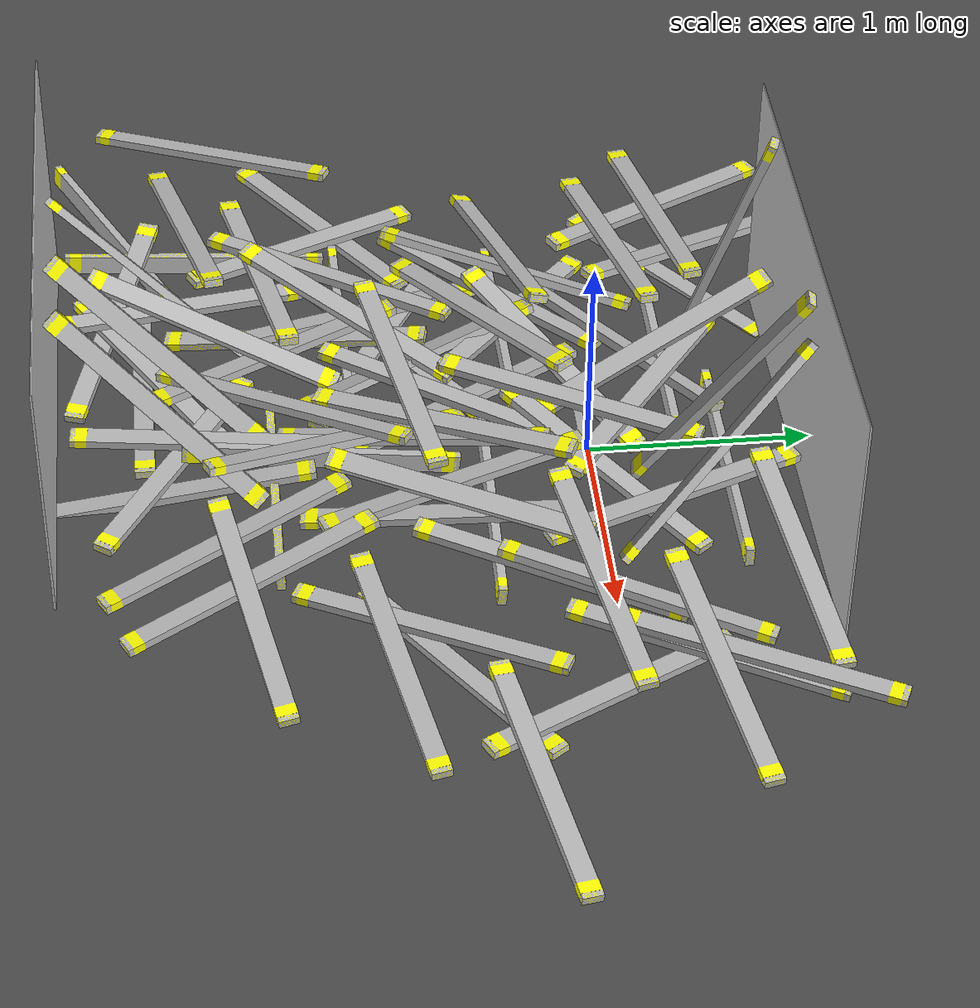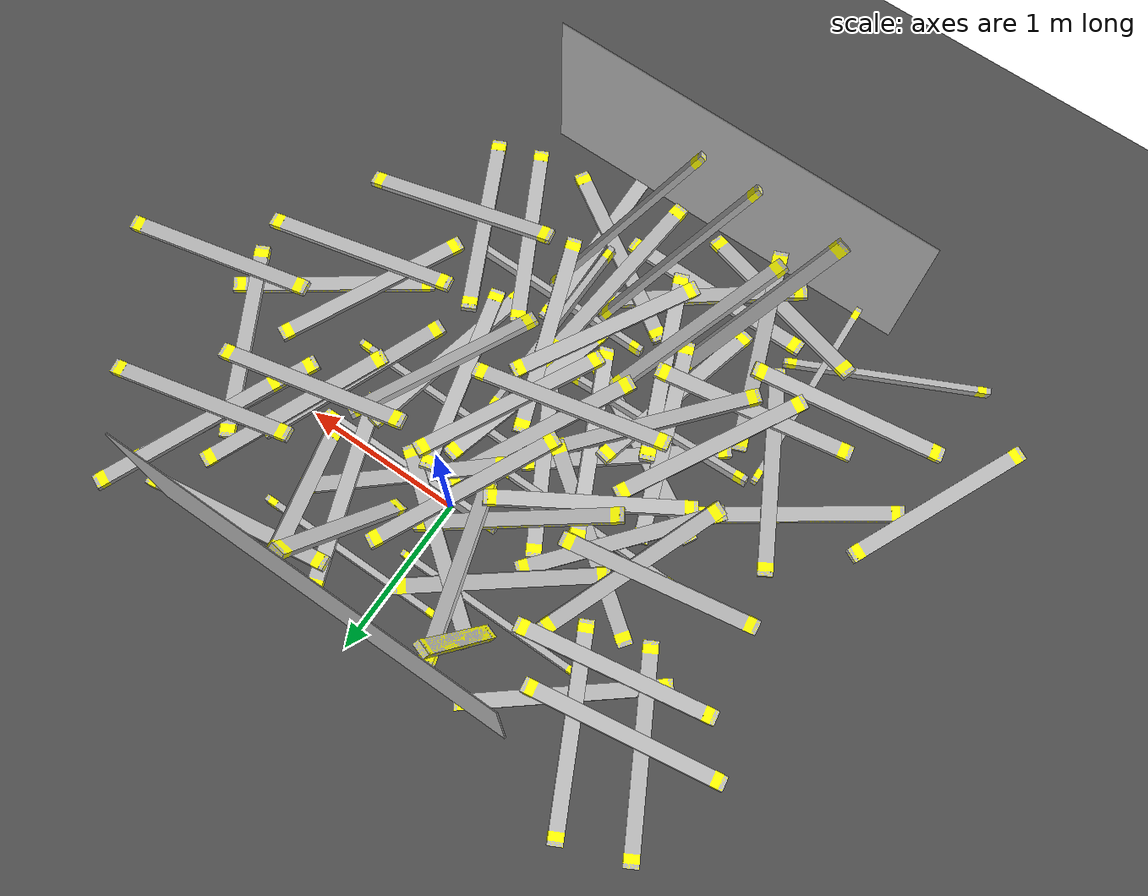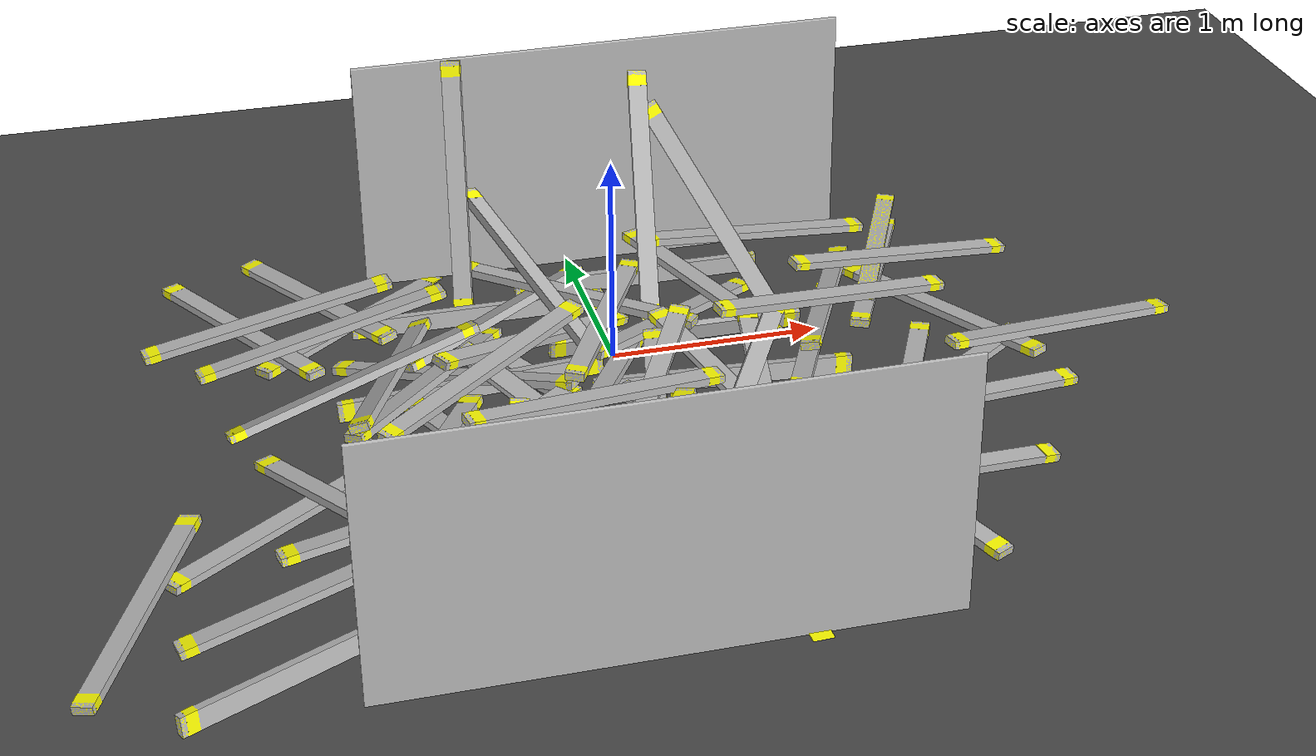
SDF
<sdf version="1.6">
 <world name="default">
  <light name="sun" type="directional">
   <pose>0 0 10 0 -0 0</pose>
   <diffuse>0.8 0.8 0.8 1</diffuse>
   <specular>0.1 0.1 0.1 1</specular>
   <attenuation>
    <range>1000</range>
    <constant>0.9</constant>
    <linear>0.01</linear>
    <quadratic>0.001</quadratic>
   </attenuation>
   <direction>-0.5 0.5 -1</direction>
  </light>
  <model name="ground_plane">
   <static>1</static>
   <link name="link">
    <collision name="collision">
     <geometry><plane><normal>0 0 1</normal><size>100 100</size></plane></geometry>
     <surface><friction><ode><mu>100</mu><mu2>50</mu2></ode></friction></surface>
    </collision>
    <visual name="visual">
     <cast_shadows>0</cast_shadows>
     <geometry><plane><normal>0 0 1</normal><size>100 100</size></plane></geometry>
     <material>
      <script><uri>file://media/materials/scripts/gazebo.material</uri><name>Gazebo/Grey</name></script>
     </material>
    </visual>
   </link>
  </model>
  <gravity>0 0 -9.8</gravity>
  <magnetic_field>6e-06 2.3e-05 -4.2e-05</magnetic_field>
  <atmosphere type="adiabatic"/>
  <physics name="default_physics" default="0" type="ode">
   <max_step_size>0.001</max_step_size>
   <real_time_factor>1</real_time_factor>
   <real_time_update_rate>1000</real_time_update_rate>
  </physics>
  <scene><ambient>0.4 0.4 0.4 1</ambient><background>0.7 0.7 0.7 1</background><shadows>1</shadows></scene>
  <spherical_coordinates>
   <surface_model>EARTH_WGS84</surface_model>
   <latitude_deg>0</latitude_deg>
   <longitude_deg>0</longitude_deg>
   <elevation>0</elevation>
   <heading_deg>0</heading_deg>
  </spherical_coordinates>
  <model name="asphalt_plane">
   <static>1</static>
   <link name="link">
    <collision name="collision"><geometry><box><size>20 20 0.1</size></box></geometry></collision>
    <visual name="visual">
     <cast_shadows>0</cast_shadows>
     <geometry><box><size>20 20 0.1</size></box></geometry>
     <material>
      <script>
       <uri>model://asphalt_plane/materials/scripts</uri>
       <uri>model://asphalt_plane/materials/textures</uri>
       <name>vrc/asphalt</name>
      </script>
     </material>
    </visual>
   </link>
   <pose>0.013797 -0.037077 0 0 -0 0</pose>
  </model>
  <model name="nist_maze_wall_240">
   <static>1</static>
   <link name="nist__maze_wall_240_link">
    <collision name="collision">
     <geometry>
      <mesh><uri>model://nist_maze_wall_240/meshes/nist_maze_wall_240.dae</uri><scale>1 1 1</scale></mesh>
     </geometry>
    </collision>
    <visual name="visual">
     <geometry>
      <mesh><uri>model://nist_maze_wall_240/meshes/nist_maze_wall_240.dae</uri><scale>1 1 1</scale></mesh>
     </geometry>
    </visual>
   </link>
   <pose>1.36498 0.295254 0.622091 3.14159 -1.56495 3.14159</pose>
  </model>
  <model name="nist_maze_wall_240_clone">
   <static>1</static>
   <link name="nist__maze_wall_240_link">
    <collision name="collision">
     <geometry>
      <mesh><uri>model://nist_maze_wall_240/meshes/nist_maze_wall_240.dae</uri><scale>1 1 1</scale></mesh>
     </geometry>
    </collision>
    <visual name="visual">
     <geometry>
      <mesh><uri>model://nist_maze_wall_240/meshes/nist_maze_wall_240.dae</uri><scale>1 1 1</scale></mesh>
     </geometry>
    </visual>
   </link>
   <pose>0.867042 -2.96104 0.6203 3.14159 -1.56495 3.14159</pose>
  </model>
  <model name="lumber_2x4x48">
   <link name="link">
    <inertial>
     <mass>1.4111</mass>
     <inertia><ixx>0.0011</ixx><ixy>0</ixy><ixz>0</ixz><iyy>0.1771</iyy><iyz>0</iyz><izz>0.1763</izz></inertia>
    </inertial>
    <collision name="collision">
     <geometry><box><size>1.2192 0.038 0.0888</size></box></geometry>
     <surface>
      <bounce><restitution_coefficient>0.01</restitution_coefficient><threshold>5</threshold></bounce>
      <friction><ode><mu>5</mu><mu2>5</mu2></ode></friction>
      <contact>
       <ode>
        <soft_cfm>0.001</soft_cfm>
        <kp>10000</kp>
        <kd>1000</kd>
        <max_vel>0.01</max_vel>
        <min_depth>0.001</min_depth>
       </ode>
      </contact>
     </surface>
    </collision>
    <visual name="visual">
     <geometry><mesh><uri>model://drc_practice_2x4/meshes/2x4x48.dae</uri><scale>1 1 1</scale></mesh></geometry>
    </visual>
   </link>
   <pose>0.299809 -0.022151 0.093348 0.216763 -0.000303 0.002883</pose>
  </model>
  <model name="lumber_2x4x48_clone">
   <link name="link">
    <inertial>
     <mass>1.4111</mass>
     <inertia><ixx>0.0011</ixx><ixy>0</ixy><ixz>0</ixz><iyy>0.1771</iyy><iyz>0</iyz><izz>0.1763</izz></inertia>
    </inertial>
    <collision name="collision">
     <geometry><box><size>1.2192 0.038 0.0888</size></box></geometry>
     <surface>
      <bounce><restitution_coefficient>0.01</restitution_coefficient><threshold>5</threshold></bounce>
      <friction><ode><mu>5</mu><mu2>5</mu2></ode></friction>
      <contact>
       <ode>
        <soft_cfm>0.001</soft_cfm>
        <kp>10000</kp>
        <kd>1000</kd>
        <max_vel>0.01</max_vel>
        <min_depth>0.001</min_depth>
       </ode>
      </contact>
     </surface>
    </collision>
    <visual name="visual">
     <geometry><mesh><uri>model://drc_practice_2x4/meshes/2x4x48.dae</uri><scale>1 1 1</scale></mesh></geometry>
    </visual>
   </link>
   <pose>-0.565985 0.393195 0.092503 -0.030887 -0.001061 -0.000131</pose>
  </model>
  <model name="lumber_2x4x48_clone_0">
   <link name="link">
    <inertial>
     <mass>1.4111</mass>
     <inertia><ixx>0.0011</ixx><ixy>0</ixy><ixz>0</ixz><iyy>0.1771</iyy><iyz>0</iyz><izz>0.1763</izz></inertia>
    </inertial>
    <collision name="collision">
     <geometry><box><size>1.2192 0.038 0.0888</size></box></geometry>
     <surface>
      <bounce><restitution_coefficient>0.01</restitution_coefficient><threshold>5</threshold></bounce>
      <friction><ode><mu>5</mu><mu2>5</mu2></ode></friction>
      <contact>
       <ode>
        <soft_cfm>0.001</soft_cfm>
        <kp>10000</kp>
        <kd>1000</kd>
        <max_vel>0.01</max_vel>
        <min_depth>0.001</min_depth>
       </ode>
      </contact>
     </surface>
    </collision>
    <visual name="visual">
     <geometry><mesh><uri>model://drc_practice_2x4/meshes/2x4x48.dae</uri><scale>1 1 1</scale></mesh></geometry>
    </visual>
   </link>
   <pose>-0.734982 -0.323296 0.127238 -0.050361 -0.058179 0.009238</pose>
  </model>
  <model name="lumber_2x4x48_clone_1">
   <link name="link">
    <inertial>
     <mass>1.4111</mass>
     <inertia><ixx>0.0011</ixx><ixy>0</ixy><ixz>0</ixz><iyy>0.1771</iyy><iyz>0</iyz><izz>0.1763</izz></inertia>
    </inertial>
    <collision name="collision">
     <geometry><box><size>1.2192 0.038 0.0888</size></box></geometry>
     <surface>
      <bounce><restitution_coefficient>0.01</restitution_coefficient><threshold>5</threshold></bounce>
      <friction><ode><mu>5</mu><mu2>5</mu2></ode></friction>
      <contact>
       <ode>
        <soft_cfm>0.001</soft_cfm>
        <kp>10000</kp>
        <kd>1000</kd>
        <max_vel>0.01</max_vel>
        <min_depth>0.001</min_depth>
       </ode>
      </contact>
     </surface>
    </collision>
    <visual name="visual">
     <geometry><mesh><uri>model://drc_practice_2x4/meshes/2x4x48.dae</uri><scale>1 1 1</scale></mesh></geometry>
    </visual>
   </link>
   <pose>0.260186 0.579401 0.09277 -0.01427 -0.000237 0.001057</pose>
  </model>
  <model name="lumber_2x4x48_clone_2">
   <link name="link">
    <inertial>
     <mass>1.4111</mass>
     <inertia><ixx>0.0011</ixx><ixy>0</ixy><ixz>0</ixz><iyy>0.1771</iyy><iyz>0</iyz><izz>0.1763</izz></inertia>
    </inertial>
    <collision name="collision">
     <geometry><box><size>1.2192 0.038 0.0888</size></box></geometry>
     <surface>
      <bounce><restitution_coefficient>0.01</restitution_coefficient><threshold>5</threshold></bounce>
      <friction><ode><mu>5</mu><mu2>5</mu2></ode></friction>
      <contact>
       <ode>
        <soft_cfm>0.001</soft_cfm>
        <kp>10000</kp>
        <kd>1000</kd>
        <max_vel>0.01</max_vel>
        <min_depth>0.001</min_depth>
       </ode>
      </contact>
     </surface>
    </collision>
    <visual name="visual">
     <geometry><mesh><uri>model://drc_practice_2x4/meshes/2x4x48.dae</uri><scale>1 1 1</scale></mesh></geometry>
    </visual>
   </link>
   <pose>0.40343 -0.479826 0.106397 -0.072152 0.025249 -0.0211</pose>
  </model>
  <model name="lumber_2x4x48_clone_3">
   <link name="link">
    <inertial>
     <mass>1.4111</mass>
     <inertia><ixx>0.0011</ixx><ixy>0</ixy><ixz>0</ixz><iyy>0.1771</iyy><iyz>0</iyz><izz>0.1763</izz></inertia>
    </inertial>
    <collision name="collision">
     <geometry><box><size>1.2192 0.038 0.0888</size></box></geometry>
     <surface>
      <bounce><restitution_coefficient>0.01</restitution_coefficient><threshold>5</threshold></bounce>
      <friction><ode><mu>5</mu><mu2>5</mu2></ode></friction>
      <contact>
       <ode>
        <soft_cfm>0.001</soft_cfm>
        <kp>10000</kp>
        <kd>1000</kd>
        <max_vel>0.01</max_vel>
        <min_depth>0.001</min_depth>
       </ode>
      </contact>
     </surface>
    </collision>
    <visual name="visual">
     <geometry><mesh><uri>model://drc_practice_2x4/meshes/2x4x48.dae</uri><scale>1 1 1</scale></mesh></geometry>
    </visual>
   </link>
   <pose>-0.803257 -0.253167 0.160232 1.47178 -0.148595 -0.631802</pose>
  </model>
  <model name="lumber_2x4x48_clone_3_clone">
   <link name="link">
    <inertial>
     <mass>1.4111</mass>
     <inertia><ixx>0.0011</ixx><ixy>0</ixy><ixz>0</ixz><iyy>0.1771</iyy><iyz>0</iyz><izz>0.1763</izz></inertia>
    </inertial>
    <collision name="collision">
     <geometry><box><size>1.2192 0.038 0.0888</size></box></geometry>
     <surface>
      <bounce><restitution_coefficient>0.01</restitution_coefficient><threshold>5</threshold></bounce>
      <friction><ode><mu>5</mu><mu2>5</mu2></ode></friction>
      <contact>
       <ode>
        <soft_cfm>0.001</soft_cfm>
        <kp>10000</kp>
        <kd>1000</kd>
        <max_vel>0.01</max_vel>
        <min_depth>0.001</min_depth>
       </ode>
      </contact>
     </surface>
    </collision>
    <visual name="visual">
     <geometry><mesh><uri>model://drc_practice_2x4/meshes/2x4x48.dae</uri><scale>1 1 1</scale></mesh></geometry>
    </visual>
   </link>
   <pose>-0.116595 0.25156 0.213472 1.50046 0.031697 -0.657545</pose>
  </model>
  <model name="lumber_2x4x48_clone_3_clone_0">
   <link name="link">
    <inertial>
     <mass>1.4111</mass>
     <inertia><ixx>0.0011</ixx><ixy>0</ixy><ixz>0</ixz><iyy>0.1771</iyy><iyz>0</iyz><izz>0.1763</izz></inertia>
    </inertial>
    <collision name="collision">
     <geometry><box><size>1.2192 0.038 0.0888</size></box></geometry>
     <surface>
      <bounce><restitution_coefficient>0.01</restitution_coefficient><threshold>5</threshold></bounce>
      <friction><ode><mu>5</mu><mu2>5</mu2></ode></friction>
      <contact>
       <ode>
        <soft_cfm>0.001</soft_cfm>
        <kp>10000</kp>
        <kd>1000</kd>
        <max_vel>0.01</max_vel>
        <min_depth>0.001</min_depth>
       </ode>
      </contact>
     </surface>
    </collision>
    <visual name="visual">
     <geometry><mesh><uri>model://drc_practice_2x4/meshes/2x4x48.dae</uri><scale>1 1 1</scale></mesh></geometry>
    </visual>
   </link>
   <pose>-0.522588 0.209963 0.170522 1.23433 0.0071 0.662603</pose>
  </model>
  <model name="lumber_2x4x48_clone_3_clone_0_clone">
   <link name="link">
    <inertial>
     <mass>1.4111</mass>
     <inertia><ixx>0.0011</ixx><ixy>0</ixy><ixz>0</ixz><iyy>0.1771</iyy><iyz>0</iyz><izz>0.1763</izz></inertia>
    </inertial>
    <collision name="collision">
     <geometry><box><size>1.2192 0.038 0.0888</size></box></geometry>
     <surface>
      <bounce><restitution_coefficient>0.01</restitution_coefficient><threshold>5</threshold></bounce>
      <friction><ode><mu>5</mu><mu2>5</mu2></ode></friction>
      <contact>
       <ode>
        <soft_cfm>0.001</soft_cfm>
        <kp>10000</kp>
        <kd>1000</kd>
        <max_vel>0.01</max_vel>
        <min_depth>0.001</min_depth>
       </ode>
      </contact>
     </surface>
    </collision>
    <visual name="visual">
     <geometry><mesh><uri>model://drc_practice_2x4/meshes/2x4x48.dae</uri><scale>1 1 1</scale></mesh></geometry>
    </visual>
   </link>
   <pose>-0.399518 -0.116983 0.215549 1.67306 0.220219 0.589613</pose>
  </model>
  <model name="lumber_2x4x48_clone_3_clone_0_clone_0">
   <link name="link">
    <inertial>
     <mass>1.4111</mass>
     <inertia><ixx>0.0011</ixx><ixy>0</ixy><ixz>0</ixz><iyy>0.1771</iyy><iyz>0</iyz><izz>0.1763</izz></inertia>
    </inertial>
    <collision name="collision">
     <geometry><box><size>1.2192 0.038 0.0888</size></box></geometry>
     <surface>
      <bounce><restitution_coefficient>0.01</restitution_coefficient><threshold>5</threshold></bounce>
      <friction><ode><mu>5</mu><mu2>5</mu2></ode></friction>
      <contact>
       <ode>
        <soft_cfm>0.001</soft_cfm>
        <kp>10000</kp>
        <kd>1000</kd>
        <max_vel>0.01</max_vel>
        <min_depth>0.001</min_depth>
       </ode>
      </contact>
     </surface>
    </collision>
    <visual name="visual">
     <geometry><mesh><uri>model://drc_practice_2x4/meshes/2x4x48.dae</uri><scale>1 1 1</scale></mesh></geometry>
    </visual>
   </link>
   <pose>0.294475 0.029636 0.150905 1.51378 0.133494 0.678541</pose>
  </model>
  <model name="lumber_2x4x48_clone_3_clone_0_clone_1">
   <link name="link">
    <inertial>
     <mass>1.4111</mass>
     <inertia><ixx>0.0011</ixx><ixy>0</ixy><ixz>0</ixz><iyy>0.1771</iyy><iyz>0</iyz><izz>0.1763</izz></inertia>
    </inertial>
    <collision name="collision">
     <geometry><box><size>1.2192 0.038 0.0888</size></box></geometry>
     <surface>
      <bounce><restitution_coefficient>0.01</restitution_coefficient><threshold>5</threshold></bounce>
      <friction><ode><mu>5</mu><mu2>5</mu2></ode></friction>
      <contact>
       <ode>
        <soft_cfm>0.001</soft_cfm>
        <kp>10000</kp>
        <kd>1000</kd>
        <max_vel>0.01</max_vel>
        <min_depth>0.001</min_depth>
       </ode>
      </contact>
     </surface>
    </collision>
    <visual name="visual">
     <geometry><mesh><uri>model://drc_practice_2x4/meshes/2x4x48.dae</uri><scale>1 1 1</scale></mesh></geometry>
    </visual>
   </link>
   <pose>-0.595379 0.66833 0.634015 1.37252 -1.24634 1.43251</pose>
  </model>
  <model name="lumber_2x4x48_clone_1_clone">
   <link name="link">
    <inertial>
     <mass>1.4111</mass>
     <inertia><ixx>0.0011</ixx><ixy>0</ixy><ixz>0</ixz><iyy>0.1771</iyy><iyz>0</iyz><izz>0.1763</izz></inertia>
    </inertial>
    <collision name="collision">
     <geometry><box><size>1.2192 0.038 0.0888</size></box></geometry>
     <surface>
      <bounce><restitution_coefficient>0.01</restitution_coefficient><threshold>5</threshold></bounce>
      <friction><ode><mu>5</mu><mu2>5</mu2></ode></friction>
      <contact>
       <ode>
        <soft_cfm>0.001</soft_cfm>
        <kp>10000</kp>
        <kd>1000</kd>
        <max_vel>0.01</max_vel>
        <min_depth>0.001</min_depth>
       </ode>
      </contact>
     </surface>
    </collision>
    <visual name="visual">
     <geometry><mesh><uri>model://drc_practice_2x4/meshes/2x4x48.dae</uri><scale>1 1 1</scale></mesh></geometry>
    </visual>
   </link>
   <pose>-0.54045 -1.96689 0.067655 -1.5708 -0 -0.002209</pose>
  </model>
  <model name="lumber_2x4x48_clone_3_clone_0_clone_0_clone">
   <link name="link">
    <inertial>
     <mass>1.4111</mass>
     <inertia><ixx>0.0011</ixx><ixy>0</ixy><ixz>0</ixz><iyy>0.1771</iyy><iyz>0</iyz><izz>0.1763</izz></inertia>
    </inertial>
    <collision name="collision">
     <geometry><box><size>1.2192 0.038 0.0888</size></box></geometry>
     <surface>
      <bounce><restitution_coefficient>0.01</restitution_coefficient><threshold>5</threshold></bounce>
      <friction><ode><mu>5</mu><mu2>5</mu2></ode></friction>
      <contact>
       <ode>
        <soft_cfm>0.001</soft_cfm>
        <kp>10000</kp>
        <kd>1000</kd>
        <max_vel>0.01</max_vel>
        <min_depth>0.001</min_depth>
       </ode>
      </contact>
     </surface>
    </collision>
    <visual name="visual">
     <geometry><mesh><uri>model://drc_practice_2x4/meshes/2x4x48.dae</uri><scale>1 1 1</scale></mesh></geometry>
    </visual>
   </link>
   <pose>-0.498556 -1.8932 0.144119 1.61509 0.125647 0.601302</pose>
  </model>
  <model name="lumber_2x4x48_clone_3_clone_0_clone_0_clone_0">
   <link name="link">
    <inertial>
     <mass>1.4111</mass>
     <inertia><ixx>0.0011</ixx><ixy>0</ixy><ixz>0</ixz><iyy>0.1771</iyy><iyz>0</iyz><izz>0.1763</izz></inertia>
    </inertial>
    <collision name="collision">
     <geometry><box><size>1.2192 0.038 0.0888</size></box></geometry>
     <surface>
      <bounce><restitution_coefficient>0.01</restitution_coefficient><threshold>5</threshold></bounce>
      <friction><ode><mu>5</mu><mu2>5</mu2></ode></friction>
      <contact>
       <ode>
        <soft_cfm>0.001</soft_cfm>
        <kp>10000</kp>
        <kd>1000</kd>
        <max_vel>0.01</max_vel>
        <min_depth>0.001</min_depth>
       </ode>
      </contact>
     </surface>
    </collision>
    <visual name="visual">
     <geometry><mesh><uri>model://drc_practice_2x4/meshes/2x4x48.dae</uri><scale>1 1 1</scale></mesh></geometry>
    </visual>
   </link>
   <pose>0.068638 -1.83077 0.128017 1.61887 -0.029542 2.5735</pose>
  </model>
  <model name="lumber_2x4x48_clone_3_clone_0_clone_0_clone_0_clone">
   <link name="link">
    <inertial>
     <mass>1.4111</mass>
     <inertia><ixx>0.0011</ixx><ixy>0</ixy><ixz>0</ixz><iyy>0.1771</iyy><iyz>0</iyz><izz>0.1763</izz></inertia>
    </inertial>
    <collision name="collision">
     <geometry><box><size>1.2192 0.038 0.0888</size></box></geometry>
     <surface>
      <bounce><restitution_coefficient>0.01</restitution_coefficient><threshold>5</threshold></bounce>
      <friction><ode><mu>5</mu><mu2>5</mu2></ode></friction>
      <contact>
       <ode>
        <soft_cfm>0.001</soft_cfm>
        <kp>10000</kp>
        <kd>1000</kd>
        <max_vel>0.01</max_vel>
        <min_depth>0.001</min_depth>
       </ode>
      </contact>
     </surface>
    </collision>
    <visual name="visual">
     <geometry><mesh><uri>model://drc_practice_2x4/meshes/2x4x48.dae</uri><scale>1 1 1</scale></mesh></geometry>
    </visual>
   </link>
   <pose>-0.907543 -2.09362 0.171348 1.59943 -0.171336 2.82423</pose>
  </model>
  <model name="lumber_2x4x48_clone_3_clone_0_clone_0_clone_0_clone_0">
   <link name="link">
    <inertial>
     <mass>1.4111</mass>
     <inertia><ixx>0.0011</ixx><ixy>0</ixy><ixz>0</ixz><iyy>0.1771</iyy><iyz>0</iyz><izz>0.1763</izz></inertia>
    </inertial>
    <collision name="collision">
     <geometry><box><size>1.2192 0.038 0.0888</size></box></geometry>
     <surface>
      <bounce><restitution_coefficient>0.01</restitution_coefficient><threshold>5</threshold></bounce>
      <friction><ode><mu>5</mu><mu2>5</mu2></ode></friction>
      <contact>
       <ode>
        <soft_cfm>0.001</soft_cfm>
        <kp>10000</kp>
        <kd>1000</kd>
        <max_vel>0.01</max_vel>
        <min_depth>0.001</min_depth>
       </ode>
      </contact>
     </surface>
    </collision>
    <visual name="visual">
     <geometry><mesh><uri>model://drc_practice_2x4/meshes/2x4x48.dae</uri><scale>1 1 1</scale></mesh></geometry>
    </visual>
   </link>
   <pose>-0.726265 -0.90114 0.062275 1.61637 -0.001409 2.62908</pose>
  </model>
  <model name="lumber_2x4x48_clone_0_clone">
   <link name="link">
    <inertial>
     <mass>1.4111</mass>
     <inertia><ixx>0.0011</ixx><ixy>0</ixy><ixz>0</ixz><iyy>0.1771</iyy><iyz>0</iyz><izz>0.1763</izz></inertia>
    </inertial>
    <collision name="collision">
     <geometry><box><size>1.2192 0.038 0.0888</size></box></geometry>
     <surface>
      <bounce><restitution_coefficient>0.01</restitution_coefficient><threshold>5</threshold></bounce>
      <friction><ode><mu>5</mu><mu2>5</mu2></ode></friction>
      <contact>
       <ode>
        <soft_cfm>0.001</soft_cfm>
        <kp>10000</kp>
        <kd>1000</kd>
        <max_vel>0.01</max_vel>
        <min_depth>0.001</min_depth>
       </ode>
      </contact>
     </surface>
    </collision>
    <visual name="visual">
     <geometry><mesh><uri>model://drc_practice_2x4/meshes/2x4x48.dae</uri><scale>1 1 1</scale></mesh></geometry>
    </visual>
   </link>
   <pose>-0.722662 -1.04605 0.133214 0.010439 0.06446 0.012369</pose>
  </model>
  <model name="lumber_2x4x48_clone_0_clone_0">
   <link name="link">
    <inertial>
     <mass>1.4111</mass>
     <inertia><ixx>0.0011</ixx><ixy>0</ixy><ixz>0</ixz><iyy>0.1771</iyy><iyz>0</iyz><izz>0.1763</izz></inertia>
    </inertial>
    <collision name="collision">
     <geometry><box><size>1.2192 0.038 0.0888</size></box></geometry>
     <surface>
      <bounce><restitution_coefficient>0.01</restitution_coefficient><threshold>5</threshold></bounce>
      <friction><ode><mu>5</mu><mu2>5</mu2></ode></friction>
      <contact>
       <ode>
        <soft_cfm>0.001</soft_cfm>
        <kp>10000</kp>
        <kd>1000</kd>
        <max_vel>0.01</max_vel>
        <min_depth>0.001</min_depth>
       </ode>
      </contact>
     </surface>
    </collision>
    <visual name="visual">
     <geometry><mesh><uri>model://drc_practice_2x4/meshes/2x4x48.dae</uri><scale>1 1 1</scale></mesh></geometry>
    </visual>
   </link>
   <pose>0.227233 -1.40603 0.089349 0.029567 0.000624 -0.008838</pose>
  </model>
  <model name="lumber_2x4x48_clone_3_clone_0_clone_1_clone">
   <link name="link">
    <inertial>
     <mass>1.4111</mass>
     <inertia><ixx>0.0011</ixx><ixy>0</ixy><ixz>0</ixz><iyy>0.1771</iyy><iyz>0</iyz><izz>0.1763</izz></inertia>
    </inertial>
    <collision name="collision">
     <geometry><box><size>1.2192 0.038 0.0888</size></box></geometry>
     <surface>
      <bounce><restitution_coefficient>0.01</restitution_coefficient><threshold>5</threshold></bounce>
      <friction><ode><mu>5</mu><mu2>5</mu2></ode></friction>
      <contact>
       <ode>
        <soft_cfm>0.001</soft_cfm>
        <kp>10000</kp>
        <kd>1000</kd>
        <max_vel>0.01</max_vel>
        <min_depth>0.001</min_depth>
       </ode>
      </contact>
     </surface>
    </collision>
    <visual name="visual">
     <geometry><mesh><uri>model://drc_practice_2x4/meshes/2x4x48.dae</uri><scale>1 1 1</scale></mesh></geometry>
    </visual>
   </link>
   <pose>-0.712223 -1.26616 0.160304 1.66457 -0.125165 1.35625</pose>
  </model>
  <model name="lumber_2x4x48_clone_3_clone_0_clone_1_clone_clone">
   <link name="link">
    <inertial>
     <mass>1.4111</mass>
     <inertia><ixx>0.0011</ixx><ixy>0</ixy><ixz>0</ixz><iyy>0.1771</iyy><iyz>0</iyz><izz>0.1763</izz></inertia>
    </inertial>
    <collision name="collision">
     <geometry><box><size>1.2192 0.038 0.0888</size></box></geometry>
     <surface>
      <bounce><restitution_coefficient>0.01</restitution_coefficient><threshold>5</threshold></bounce>
      <friction><ode><mu>5</mu><mu2>5</mu2></ode></friction>
      <contact>
       <ode>
        <soft_cfm>0.001</soft_cfm>
        <kp>10000</kp>
        <kd>1000</kd>
        <max_vel>0.01</max_vel>
        <min_depth>0.001</min_depth>
       </ode>
      </contact>
     </surface>
    </collision>
    <visual name="visual">
     <geometry><mesh><uri>model://drc_practice_2x4/meshes/2x4x48.dae</uri><scale>1 1 1</scale></mesh></geometry>
    </visual>
   </link>
   <pose>0.122564 -1.19447 0.156664 -0.001536 0.104658 1.54007</pose>
  </model>
  <model name="lumber_2x4x48_clone_3_clone_0_clone_1_clone_clone_0">
   <link name="link">
    <inertial>
     <mass>1.4111</mass>
     <inertia><ixx>0.0011</ixx><ixy>0</ixy><ixz>0</ixz><iyy>0.1771</iyy><iyz>0</iyz><izz>0.1763</izz></inertia>
    </inertial>
    <collision name="collision">
     <geometry><box><size>1.2192 0.038 0.0888</size></box></geometry>
     <surface>
      <bounce><restitution_coefficient>0.01</restitution_coefficient><threshold>5</threshold></bounce>
      <friction><ode><mu>5</mu><mu2>5</mu2></ode></friction>
      <contact>
       <ode>
        <soft_cfm>0.001</soft_cfm>
        <kp>10000</kp>
        <kd>1000</kd>
        <max_vel>0.01</max_vel>
        <min_depth>0.001</min_depth>
       </ode>
      </contact>
     </surface>
    </collision>
    <visual name="visual">
     <geometry><mesh><uri>model://drc_practice_2x4/meshes/2x4x48.dae</uri><scale>1 1 1</scale></mesh></geometry>
    </visual>
   </link>
   <pose>0.521841 -0.706496 0.138551 1.61232 -0.114029 1.40547</pose>
  </model>
  <model name="lumber_2x4x48_clone_3_clone_0_clone_1_clone_clone_1">
   <link name="link">
    <inertial>
     <mass>1.4111</mass>
     <inertia><ixx>0.0011</ixx><ixy>0</ixy><ixz>0</ixz><iyy>0.1771</iyy><iyz>0</iyz><izz>0.1763</izz></inertia>
    </inertial>
    <collision name="collision">
     <geometry><box><size>1.2192 0.038 0.0888</size></box></geometry>
     <surface>
      <bounce><restitution_coefficient>0.01</restitution_coefficient><threshold>5</threshold></bounce>
      <friction><ode><mu>5</mu><mu2>5</mu2></ode></friction>
      <contact>
       <ode>
        <soft_cfm>0.001</soft_cfm>
        <kp>10000</kp>
        <kd>1000</kd>
        <max_vel>0.01</max_vel>
        <min_depth>0.001</min_depth>
       </ode>
      </contact>
     </surface>
    </collision>
    <visual name="visual">
     <geometry><mesh><uri>model://drc_practice_2x4/meshes/2x4x48.dae</uri><scale>1 1 1</scale></mesh></geometry>
    </visual>
   </link>
   <pose>-1.33411 -1.70498 0.152795 3.10277 0.099878 1.61615</pose>
  </model>
  <model name="lumber_2x4x48_clone_3_clone_0_clone_1_clone_clone_2">
   <link name="link">
    <inertial>
     <mass>1.4111</mass>
     <inertia><ixx>0.0011</ixx><ixy>0</ixy><ixz>0</ixz><iyy>0.1771</iyy><iyz>0</iyz><izz>0.1763</izz></inertia>
    </inertial>
    <collision name="collision">
     <geometry><box><size>1.2192 0.038 0.0888</size></box></geometry>
     <surface>
      <bounce><restitution_coefficient>0.01</restitution_coefficient><threshold>5</threshold></bounce>
      <friction><ode><mu>5</mu><mu2>5</mu2></ode></friction>
      <contact>
       <ode>
        <soft_cfm>0.001</soft_cfm>
        <kp>10000</kp>
        <kd>1000</kd>
        <max_vel>0.01</max_vel>
        <min_depth>0.001</min_depth>
       </ode>
      </contact>
     </surface>
    </collision>
    <visual name="visual">
     <geometry><mesh><uri>model://drc_practice_2x4/meshes/2x4x48.dae</uri><scale>1 1 1</scale></mesh></geometry>
    </visual>
   </link>
   <pose>-1.65672 -2.09284 0.091985 -0.102749 0.002228 0.448588</pose>
  </model>
  <model name="lumber_2x4x48_clone_3_clone_0_clone_clone">
   <link name="link">
    <inertial>
     <mass>1.4111</mass>
     <inertia><ixx>0.0011</ixx><ixy>0</ixy><ixz>0</ixz><iyy>0.1771</iyy><iyz>0</iyz><izz>0.1763</izz></inertia>
    </inertial>
    <collision name="collision">
     <geometry><box><size>1.2192 0.038 0.0888</size></box></geometry>
     <surface>
      <bounce><restitution_coefficient>0.01</restitution_coefficient><threshold>5</threshold></bounce>
      <friction><ode><mu>5</mu><mu2>5</mu2></ode></friction>
      <contact>
       <ode>
        <soft_cfm>0.001</soft_cfm>
        <kp>10000</kp>
        <kd>1000</kd>
        <max_vel>0.01</max_vel>
        <min_depth>0.001</min_depth>
       </ode>
      </contact>
     </surface>
    </collision>
    <visual name="visual">
     <geometry><mesh><uri>model://drc_practice_2x4/meshes/2x4x48.dae</uri><scale>1 1 1</scale></mesh></geometry>
    </visual>
   </link>
   <pose>-1.67648 -1.09313 0.067386 1.56472 -0.000436 0.618188</pose>
  </model>
  <model name="lumber_2x4x48_clone_3_clone_0_clone_clone_0">
   <link name="link">
    <inertial>
     <mass>1.4111</mass>
     <inertia><ixx>0.0011</ixx><ixy>0</ixy><ixz>0</ixz><iyy>0.1771</iyy><iyz>0</iyz><izz>0.1763</izz></inertia>
    </inertial>
    <collision name="collision">
     <geometry><box><size>1.2192 0.038 0.0888</size></box></geometry>
     <surface>
      <bounce><restitution_coefficient>0.01</restitution_coefficient><threshold>5</threshold></bounce>
      <friction><ode><mu>5</mu><mu2>5</mu2></ode></friction>
      <contact>
       <ode>
        <soft_cfm>0.001</soft_cfm>
        <kp>10000</kp>
        <kd>1000</kd>
        <max_vel>0.01</max_vel>
        <min_depth>0.001</min_depth>
       </ode>
      </contact>
     </surface>
    </collision>
    <visual name="visual">
     <geometry><mesh><uri>model://drc_practice_2x4/meshes/2x4x48.dae</uri><scale>1 1 1</scale></mesh></geometry>
    </visual>
   </link>
   <pose>1.3955 -0.708259 0.066325 1.55393 0.000566 0.618301</pose>
  </model>
  <model name="lumber_2x4x48_clone_3_clone_0_clone_clone_0_clone">
   <link name="link">
    <inertial>
     <mass>1.4111</mass>
     <inertia><ixx>0.0011</ixx><ixy>0</ixy><ixz>0</ixz><iyy>0.1771</iyy><iyz>0</iyz><izz>0.1763</izz></inertia>
    </inertial>
    <collision name="collision">
     <geometry><box><size>1.2192 0.038 0.0888</size></box></geometry>
     <surface>
      <bounce><restitution_coefficient>0.01</restitution_coefficient><threshold>5</threshold></bounce>
      <friction><ode><mu>5</mu><mu2>5</mu2></ode></friction>
      <contact>
       <ode>
        <soft_cfm>0.001</soft_cfm>
        <kp>10000</kp>
        <kd>1000</kd>
        <max_vel>0.01</max_vel>
        <min_depth>0.001</min_depth>
       </ode>
      </contact>
     </surface>
    </collision>
    <visual name="visual">
     <geometry><mesh><uri>model://drc_practice_2x4/meshes/2x4x48.dae</uri><scale>1 1 1</scale></mesh></geometry>
    </visual>
   </link>
   <pose>-0.673631 -0.80957 0.086985 1.59472 0.042096 0.660763</pose>
  </model>
  <model name="lumber_2x4x48_clone_3_clone_0_clone_1_clone_clone_3">
   <link name="link">
    <inertial>
     <mass>1.4111</mass>
     <inertia><ixx>0.0011</ixx><ixy>0</ixy><ixz>0</ixz><iyy>0.1771</iyy><iyz>0</iyz><izz>0.1763</izz></inertia>
    </inertial>
    <collision name="collision">
     <geometry><box><size>1.2192 0.038 0.0888</size></box></geometry>
     <surface>
      <bounce><restitution_coefficient>0.01</restitution_coefficient><threshold>5</threshold></bounce>
      <friction><ode><mu>5</mu><mu2>5</mu2></ode></friction>
      <contact>
       <ode>
        <soft_cfm>0.001</soft_cfm>
        <kp>10000</kp>
        <kd>1000</kd>
        <max_vel>0.01</max_vel>
        <min_depth>0.001</min_depth>
       </ode>
      </contact>
     </surface>
    </collision>
    <visual name="visual">
     <geometry><mesh><uri>model://drc_practice_2x4/meshes/2x4x48.dae</uri><scale>1 1 1</scale></mesh></geometry>
    </visual>
   </link>
   <pose>0.011224 -0.78563 0.145827 1.47225 -0.113051 1.34703</pose>
  </model>
  <model name="lumber_2x4x48_clone_3_clone_0_clone_1_clone_clone_4">
   <link name="link">
    <inertial>
     <mass>1.4111</mass>
     <inertia><ixx>0.0011</ixx><ixy>0</ixy><ixz>0</ixz><iyy>0.1771</iyy><iyz>0</iyz><izz>0.1763</izz></inertia>
    </inertial>
    <collision name="collision">
     <geometry><box><size>1.2192 0.038 0.0888</size></box></geometry>
     <surface>
      <bounce><restitution_coefficient>0.01</restitution_coefficient><threshold>5</threshold></bounce>
      <friction><ode><mu>5</mu><mu2>5</mu2></ode></friction>
      <contact>
       <ode>
        <soft_cfm>0.001</soft_cfm>
        <kp>10000</kp>
        <kd>1000</kd>
        <max_vel>0.01</max_vel>
        <min_depth>0.001</min_depth>
       </ode>
      </contact>
     </surface>
    </collision>
    <visual name="visual">
     <geometry><mesh><uri>model://drc_practice_2x4/meshes/2x4x48.dae</uri><scale>1 1 1</scale></mesh></geometry>
    </visual>
   </link>
   <pose>-1.15745 0.520069 0.050068 1.52126 0.027405 0.681696</pose>
  </model>
  <model name="lumber_2x4x48_clone_3_clone_0_clone_1_clone_0">
   <link name="link">
    <inertial>
     <mass>1.4111</mass>
     <inertia><ixx>0.0011</ixx><ixy>0</ixy><ixz>0</ixz><iyy>0.1771</iyy><iyz>0</iyz><izz>0.1763</izz></inertia>
    </inertial>
    <collision name="collision">
     <geometry><box><size>1.2192 0.038 0.0888</size></box></geometry>
     <surface>
      <bounce><restitution_coefficient>0.01</restitution_coefficient><threshold>5</threshold></bounce>
      <friction><ode><mu>5</mu><mu2>5</mu2></ode></friction>
      <contact>
       <ode>
        <soft_cfm>0.001</soft_cfm>
        <kp>10000</kp>
        <kd>1000</kd>
        <max_vel>0.01</max_vel>
        <min_depth>0.001</min_depth>
       </ode>
      </contact>
     </surface>
    </collision>
    <visual name="visual">
     <geometry><mesh><uri>model://drc_practice_2x4/meshes/2x4x48.dae</uri><scale>1 1 1</scale></mesh></geometry>
    </visual>
   </link>
   <pose>0.285411 0.522611 0.557321 1.58891 -0.955968 1.41395</pose>
  </model>
  <model name="lumber_2x4x48_clone_3_clone_0_clone_1_clone_1">
   <link name="link">
    <inertial>
     <mass>1.4111</mass>
     <inertia><ixx>0.0011</ixx><ixy>0</ixy><ixz>0</ixz><iyy>0.1771</iyy><iyz>0</iyz><izz>0.1763</izz></inertia>
    </inertial>
    <collision name="collision">
     <geometry><box><size>1.2192 0.038 0.0888</size></box></geometry>
     <surface>
      <bounce><restitution_coefficient>0.01</restitution_coefficient><threshold>5</threshold></bounce>
      <friction><ode><mu>5</mu><mu2>5</mu2></ode></friction>
      <contact>
       <ode>
        <soft_cfm>0.001</soft_cfm>
        <kp>10000</kp>
        <kd>1000</kd>
        <max_vel>0.01</max_vel>
        <min_depth>0.001</min_depth>
       </ode>
      </contact>
     </surface>
    </collision>
    <visual name="visual">
     <geometry><mesh><uri>model://drc_practice_2x4/meshes/2x4x48.dae</uri><scale>1 1 1</scale></mesh></geometry>
    </visual>
   </link>
   <pose>-0.019981 -1.68158 0.164661 -1.62173 -0.035128 -1.66607</pose>
  </model>
  <model name="lumber_2x4x48_clone_3_clone_0_clone_1_clone_2">
   <link name="link">
    <inertial>
     <mass>1.4111</mass>
     <inertia><ixx>0.0011</ixx><ixy>0</ixy><ixz>0</ixz><iyy>0.1771</iyy><iyz>0</iyz><izz>0.1763</izz></inertia>
    </inertial>
    <collision name="collision">
     <geometry><box><size>1.2192 0.038 0.0888</size></box></geometry>
     <surface>
      <bounce><restitution_coefficient>0.01</restitution_coefficient><threshold>5</threshold></bounce>
      <friction><ode><mu>5</mu><mu2>5</mu2></ode></friction>
      <contact>
       <ode>
        <soft_cfm>0.001</soft_cfm>
        <kp>10000</kp>
        <kd>1000</kd>
        <max_vel>0.01</max_vel>
        <min_depth>0.001</min_depth>
       </ode>
      </contact>
     </surface>
    </collision>
    <visual name="visual">
     <geometry><mesh><uri>model://drc_practice_2x4/meshes/2x4x48.dae</uri><scale>1 1 1</scale></mesh></geometry>
    </visual>
   </link>
   <pose>0.224885 -1.82956 0.09117 -1.56318 0.103382 -1.52226</pose>
  </model>
  <model name="lumber_2x4x48_clone_3_clone_0_clone_clone_0_clone_0">
   <link name="link">
    <inertial>
     <mass>1.4111</mass>
     <inertia><ixx>0.0011</ixx><ixy>0</ixy><ixz>0</ixz><iyy>0.1771</iyy><iyz>0</iyz><izz>0.1763</izz></inertia>
    </inertial>
    <collision name="collision">
     <geometry><box><size>1.2192 0.038 0.0888</size></box></geometry>
     <surface>
      <bounce><restitution_coefficient>0.01</restitution_coefficient><threshold>5</threshold></bounce>
      <friction><ode><mu>5</mu><mu2>5</mu2></ode></friction>
      <contact>
       <ode>
        <soft_cfm>0.001</soft_cfm>
        <kp>10000</kp>
        <kd>1000</kd>
        <max_vel>0.01</max_vel>
        <min_depth>0.001</min_depth>
       </ode>
      </contact>
     </surface>
    </collision>
    <visual name="visual">
     <geometry><mesh><uri>model://drc_practice_2x4/meshes/2x4x48.dae</uri><scale>1 1 1</scale></mesh></geometry>
    </visual>
   </link>
   <pose>-0.964717 -1.77716 0.175353 -1.65873 -0.171989 -1.19207</pose>
  </model>
  <model name="lumber_2x4x48_clone_3_clone_0_clone_clone_0_clone_0_clone">
   <link name="link">
    <inertial>
     <mass>1.4111</mass>
     <inertia><ixx>0.0011</ixx><ixy>0</ixy><ixz>0</ixz><iyy>0.1771</iyy><iyz>0</iyz><izz>0.1763</izz></inertia>
    </inertial>
    <collision name="collision">
     <geometry><box><size>1.2192 0.038 0.0888</size></box></geometry>
     <surface>
      <bounce><restitution_coefficient>0.01</restitution_coefficient><threshold>5</threshold></bounce>
      <friction><ode><mu>5</mu><mu2>5</mu2></ode></friction>
      <contact>
       <ode>
        <soft_cfm>0.001</soft_cfm>
        <kp>10000</kp>
        <kd>1000</kd>
        <max_vel>0.01</max_vel>
        <min_depth>0.001</min_depth>
       </ode>
      </contact>
     </surface>
    </collision>
    <visual name="visual">
     <geometry><mesh><uri>model://drc_practice_2x4/meshes/2x4x48.dae</uri><scale>1 1 1</scale></mesh></geometry>
    </visual>
   </link>
   <pose>0.606662 0.461635 0.473095 -0.906832 0.700177 -1.1021</pose>
  </model>
  <model name="lumber_2x4x48_clone_3_clone_0_clone_clone_0_clone_0_clone_0">
   <link name="link">
    <inertial>
     <mass>1.4111</mass>
     <inertia><ixx>0.0011</ixx><ixy>0</ixy><ixz>0</ixz><iyy>0.1771</iyy><iyz>0</iyz><izz>0.1763</izz></inertia>
    </inertial>
    <collision name="collision">
     <geometry><box><size>1.2192 0.038 0.0888</size></box></geometry>
     <surface>
      <bounce><restitution_coefficient>0.01</restitution_coefficient><threshold>5</threshold></bounce>
      <friction><ode><mu>5</mu><mu2>5</mu2></ode></friction>
      <contact>
       <ode>
        <soft_cfm>0.001</soft_cfm>
        <kp>10000</kp>
        <kd>1000</kd>
        <max_vel>0.01</max_vel>
        <min_depth>0.001</min_depth>
       </ode>
      </contact>
     </surface>
    </collision>
    <visual name="visual">
     <geometry><mesh><uri>model://drc_practice_2x4/meshes/2x4x48.dae</uri><scale>1 1 1</scale></mesh></geometry>
    </visual>
   </link>
   <pose>0.10718 -1.12676 0.227917 -1.37828 -0.109397 -1.22917</pose>
  </model>
  <model name="lumber_2x4x48_clone_3_clone_0_clone_clone_0_clone_0_clone_1">
   <link name="link">
    <inertial>
     <mass>1.4111</mass>
     <inertia><ixx>0.0011</ixx><ixy>0</ixy><ixz>0</ixz><iyy>0.1771</iyy><iyz>0</iyz><izz>0.1763</izz></inertia>
    </inertial>
    <collision name="collision">
     <geometry><box><size>1.2192 0.038 0.0888</size></box></geometry>
     <surface>
      <bounce><restitution_coefficient>0.01</restitution_coefficient><threshold>5</threshold></bounce>
      <friction><ode><mu>5</mu><mu2>5</mu2></ode></friction>
      <contact>
       <ode>
        <soft_cfm>0.001</soft_cfm>
        <kp>10000</kp>
        <kd>1000</kd>
        <max_vel>0.01</max_vel>
        <min_depth>0.001</min_depth>
       </ode>
      </contact>
     </surface>
    </collision>
    <visual name="visual">
     <geometry><mesh><uri>model://drc_practice_2x4/meshes/2x4x48.dae</uri><scale>1 1 1</scale></mesh></geometry>
    </visual>
   </link>
   <pose>-0.814711 -0.979548 0.19887 -1.45918 -0.082076 -1.20545</pose>
  </model>
  <model name="lumber_2x4x48_clone_3_clone_0_clone_clone_0_clone_0_clone_2">
   <link name="link">
    <inertial>
     <mass>1.4111</mass>
     <inertia><ixx>0.0011</ixx><ixy>0</ixy><ixz>0</ixz><iyy>0.1771</iyy><iyz>0</iyz><izz>0.1763</izz></inertia>
    </inertial>
    <collision name="collision">
     <geometry><box><size>1.2192 0.038 0.0888</size></box></geometry>
     <surface>
      <bounce><restitution_coefficient>0.01</restitution_coefficient><threshold>5</threshold></bounce>
      <friction><ode><mu>5</mu><mu2>5</mu2></ode></friction>
      <contact>
       <ode>
        <soft_cfm>0.001</soft_cfm>
        <kp>10000</kp>
        <kd>1000</kd>
        <max_vel>0.01</max_vel>
        <min_depth>0.001</min_depth>
       </ode>
      </contact>
     </surface>
    </collision>
    <visual name="visual">
     <geometry><mesh><uri>model://drc_practice_2x4/meshes/2x4x48.dae</uri><scale>1 1 1</scale></mesh></geometry>
    </visual>
   </link>
   <pose>-1.4128 -1.19466 0.159376 -1.60823 -0.092668 -1.05484</pose>
  </model>
  <model name="lumber_2x4x48_clone_3_clone_0_clone_clone_0_clone_0_clone_3">
   <link name="link">
    <inertial>
     <mass>1.4111</mass>
     <inertia><ixx>0.0011</ixx><ixy>0</ixy><ixz>0</ixz><iyy>0.1771</iyy><iyz>0</iyz><izz>0.1763</izz></inertia>
    </inertial>
    <collision name="collision">
     <geometry><box><size>1.2192 0.038 0.0888</size></box></geometry>
     <surface>
      <bounce><restitution_coefficient>0.01</restitution_coefficient><threshold>5</threshold></bounce>
      <friction><ode><mu>5</mu><mu2>5</mu2></ode></friction>
      <contact>
       <ode>
        <soft_cfm>0.001</soft_cfm>
        <kp>10000</kp>
        <kd>1000</kd>
        <max_vel>0.01</max_vel>
        <min_depth>0.001</min_depth>
       </ode>
      </contact>
     </surface>
    </collision>
    <visual name="visual">
     <geometry><mesh><uri>model://drc_practice_2x4/meshes/2x4x48.dae</uri><scale>1 1 1</scale></mesh></geometry>
    </visual>
   </link>
   <pose>0.365817 -0.638747 0.179042 -1.50341 0.094534 -1.28603</pose>
  </model>
  <model name="lumber_2x4x48_clone_3_clone_0_clone_clone_0_clone_0_clone_4">
   <link name="link">
    <inertial>
     <mass>1.4111</mass>
     <inertia><ixx>0.0011</ixx><ixy>0</ixy><ixz>0</ixz><iyy>0.1771</iyy><iyz>0</iyz><izz>0.1763</izz></inertia>
    </inertial>
    <collision name="collision">
     <geometry><box><size>1.2192 0.038 0.0888</size></box></geometry>
     <surface>
      <bounce><restitution_coefficient>0.01</restitution_coefficient><threshold>5</threshold></bounce>
      <friction><ode><mu>5</mu><mu2>5</mu2></ode></friction>
      <contact>
       <ode>
        <soft_cfm>0.001</soft_cfm>
        <kp>10000</kp>
        <kd>1000</kd>
        <max_vel>0.01</max_vel>
        <min_depth>0.001</min_depth>
       </ode>
      </contact>
     </surface>
    </collision>
    <visual name="visual">
     <geometry><mesh><uri>model://drc_practice_2x4/meshes/2x4x48.dae</uri><scale>1 1 1</scale></mesh></geometry>
    </visual>
   </link>
   <pose>0.864944 -1.53555 0.135789 -1.57089 0.112029 -1.09624</pose>
  </model>
  <model name="lumber_2x4x48_clone_3_clone_0_clone_clone_0_clone_0_clone_5">
   <link name="link">
    <inertial>
     <mass>1.4111</mass>
     <inertia><ixx>0.0011</ixx><ixy>0</ixy><ixz>0</ixz><iyy>0.1771</iyy><iyz>0</iyz><izz>0.1763</izz></inertia>
    </inertial>
    <collision name="collision">
     <geometry><box><size>1.2192 0.038 0.0888</size></box></geometry>
     <surface>
      <bounce><restitution_coefficient>0.01</restitution_coefficient><threshold>5</threshold></bounce>
      <friction><ode><mu>5</mu><mu2>5</mu2></ode></friction>
      <contact>
       <ode>
        <soft_cfm>0.001</soft_cfm>
        <kp>10000</kp>
        <kd>1000</kd>
        <max_vel>0.01</max_vel>
        <min_depth>0.001</min_depth>
       </ode>
      </contact>
     </surface>
    </collision>
    <visual name="visual">
     <geometry><mesh><uri>model://drc_practice_2x4/meshes/2x4x48.dae</uri><scale>1 1 1</scale></mesh></geometry>
    </visual>
   </link>
   <pose>1.59935 -0.109616 0.085956 -1.58206 -0.033671 -1.07877</pose>
  </model>
  <model name="lumber_2x4x48_clone_3_clone_0_clone_clone_0_clone_0_clone_6">
   <link name="link">
    <inertial>
     <mass>1.4111</mass>
     <inertia><ixx>0.0011</ixx><ixy>0</ixy><ixz>0</ixz><iyy>0.1771</iyy><iyz>0</iyz><izz>0.1763</izz></inertia>
    </inertial>
    <collision name="collision">
     <geometry><box><size>1.2192 0.038 0.0888</size></box></geometry>
     <surface>
      <bounce><restitution_coefficient>0.01</restitution_coefficient><threshold>5</threshold></bounce>
      <friction><ode><mu>5</mu><mu2>5</mu2></ode></friction>
      <contact>
       <ode>
        <soft_cfm>0.001</soft_cfm>
        <kp>10000</kp>
        <kd>1000</kd>
        <max_vel>0.01</max_vel>
        <min_depth>0.001</min_depth>
       </ode>
      </contact>
     </surface>
    </collision>
    <visual name="visual">
     <geometry><mesh><uri>model://drc_practice_2x4/meshes/2x4x48.dae</uri><scale>1 1 1</scale></mesh></geometry>
    </visual>
   </link>
   <pose>-1.68414 0.535844 0.086215 -1.57866 -0.030657 -1.06819</pose>
  </model>
  <model name="lumber_2x4x48_clone_3_clone_0_clone_clone_0_clone_0_clone_7">
   <link name="link">
    <inertial>
     <mass>1.4111</mass>
     <inertia><ixx>0.0011</ixx><ixy>0</ixy><ixz>0</ixz><iyy>0.1771</iyy><iyz>0</iyz><izz>0.1763</izz></inertia>
    </inertial>
    <collision name="collision">
     <geometry><box><size>1.2192 0.038 0.0888</size></box></geometry>
     <surface>
      <bounce><restitution_coefficient>0.01</restitution_coefficient><threshold>5</threshold></bounce>
      <friction><ode><mu>5</mu><mu2>5</mu2></ode></friction>
      <contact>
       <ode>
        <soft_cfm>0.001</soft_cfm>
        <kp>10000</kp>
        <kd>1000</kd>
        <max_vel>0.01</max_vel>
        <min_depth>0.001</min_depth>
       </ode>
      </contact>
     </surface>
    </collision>
    <visual name="visual">
     <geometry><mesh><uri>model://drc_practice_2x4/meshes/2x4x48.dae</uri><scale>1 1 1</scale></mesh></geometry>
    </visual>
   </link>
   <pose>-1.30758 0.664214 0.125964 -1.45914 -0.088117 -1.10765</pose>
  </model>
  <model name="lumber_2x4x48_clone_3_clone_0_clone_clone_0_clone_0_clone_8">
   <link name="link">
    <inertial>
     <mass>1.4111</mass>
     <inertia><ixx>0.0011</ixx><ixy>0</ixy><ixz>0</ixz><iyy>0.1771</iyy><iyz>0</iyz><izz>0.1763</izz></inertia>
    </inertial>
    <collision name="collision">
     <geometry><box><size>1.2192 0.038 0.0888</size></box></geometry>
     <surface>
      <bounce><restitution_coefficient>0.01</restitution_coefficient><threshold>5</threshold></bounce>
      <friction><ode><mu>5</mu><mu2>5</mu2></ode></friction>
      <contact>
       <ode>
        <soft_cfm>0.001</soft_cfm>
        <kp>10000</kp>
        <kd>1000</kd>
        <max_vel>0.01</max_vel>
        <min_depth>0.001</min_depth>
       </ode>
      </contact>
     </surface>
    </collision>
    <visual name="visual">
     <geometry><mesh><uri>model://drc_practice_2x4/meshes/2x4x48.dae</uri><scale>1 1 1</scale></mesh></geometry>
    </visual>
   </link>
   <pose>0.595626 -1.63115 0.12749 1.62221 0.094399 -1.07543</pose>
  </model>
  <model name="lumber_2x4x48_clone_3_clone_0_clone_clone_0_clone_0_clone_5_clone">
   <link name="link">
    <inertial>
     <mass>1.4111</mass>
     <inertia><ixx>0.0011</ixx><ixy>0</ixy><ixz>0</ixz><iyy>0.1771</iyy><iyz>0</iyz><izz>0.1763</izz></inertia>
    </inertial>
    <collision name="collision">
     <geometry><box><size>1.2192 0.038 0.0888</size></box></geometry>
     <surface>
      <bounce><restitution_coefficient>0.01</restitution_coefficient><threshold>5</threshold></bounce>
      <friction><ode><mu>5</mu><mu2>5</mu2></ode></friction>
      <contact>
       <ode>
        <soft_cfm>0.001</soft_cfm>
        <kp>10000</kp>
        <kd>1000</kd>
        <max_vel>0.01</max_vel>
        <min_depth>0.001</min_depth>
       </ode>
      </contact>
     </surface>
    </collision>
    <visual name="visual">
     <geometry><mesh><uri>model://drc_practice_2x4/meshes/2x4x48.dae</uri><scale>1 1 1</scale></mesh></geometry>
    </visual>
   </link>
   <pose>-0.280714 -0.534985 0.095877 -1.49617 0.017279 -1.05708</pose>
  </model>
  <model name="lumber_2x4x48_clone_3_clone_0_clone_clone_0_clone_0_clone_0_clone">
   <link name="link">
    <inertial>
     <mass>1.4111</mass>
     <inertia><ixx>0.0011</ixx><ixy>0</ixy><ixz>0</ixz><iyy>0.1771</iyy><iyz>0</iyz><izz>0.1763</izz></inertia>
    </inertial>
    <collision name="collision">
     <geometry><box><size>1.2192 0.038 0.0888</size></box></geometry>
     <surface>
      <bounce><restitution_coefficient>0.01</restitution_coefficient><threshold>5</threshold></bounce>
      <friction><ode><mu>5</mu><mu2>5</mu2></ode></friction>
      <contact>
       <ode>
        <soft_cfm>0.001</soft_cfm>
        <kp>10000</kp>
        <kd>1000</kd>
        <max_vel>0.01</max_vel>
        <min_depth>0.001</min_depth>
       </ode>
      </contact>
     </surface>
    </collision>
    <visual name="visual">
     <geometry><mesh><uri>model://drc_practice_2x4/meshes/2x4x48.dae</uri><scale>1 1 1</scale></mesh></geometry>
    </visual>
   </link>
   <pose>-0.479229 -0.730992 0.201368 -1.3156 0.07574 -1.11519</pose>
  </model>
  <model name="lumber_2x4x48_clone_3_clone_0_clone_clone_0_clone_0_clone_0_clone_0">
   <link name="link">
    <inertial>
     <mass>1.4111</mass>
     <inertia><ixx>0.0011</ixx><ixy>0</ixy><ixz>0</ixz><iyy>0.1771</iyy><iyz>0</iyz><izz>0.1763</izz></inertia>
    </inertial>
    <collision name="collision">
     <geometry><box><size>1.2192 0.038 0.0888</size></box></geometry>
     <surface>
      <bounce><restitution_coefficient>0.01</restitution_coefficient><threshold>5</threshold></bounce>
      <friction><ode><mu>5</mu><mu2>5</mu2></ode></friction>
      <contact>
       <ode>
        <soft_cfm>0.001</soft_cfm>
        <kp>10000</kp>
        <kd>1000</kd>
        <max_vel>0.01</max_vel>
        <min_depth>0.001</min_depth>
       </ode>
      </contact>
     </surface>
    </collision>
    <visual name="visual">
     <geometry><mesh><uri>model://drc_practice_2x4/meshes/2x4x48.dae</uri><scale>1 1 1</scale></mesh></geometry>
    </visual>
   </link>
   <pose>-0.558672 -1.36684 0.203288 -1.48474 0.068147 -1.15903</pose>
  </model>
  <model name="lumber_2x4x48_clone_3_clone_0_clone_clone_0_clone_0_clone_9">
   <link name="link">
    <inertial>
     <mass>1.4111</mass>
     <inertia><ixx>0.0011</ixx><ixy>0</ixy><ixz>0</ixz><iyy>0.1771</iyy><iyz>0</iyz><izz>0.1763</izz></inertia>
    </inertial>
    <collision name="collision">
     <geometry><box><size>1.2192 0.038 0.0888</size></box></geometry>
     <surface>
      <bounce><restitution_coefficient>0.01</restitution_coefficient><threshold>5</threshold></bounce>
      <friction><ode><mu>5</mu><mu2>5</mu2></ode></friction>
      <contact>
       <ode>
        <soft_cfm>0.001</soft_cfm>
        <kp>10000</kp>
        <kd>1000</kd>
        <max_vel>0.01</max_vel>
        <min_depth>0.001</min_depth>
       </ode>
      </contact>
     </surface>
    </collision>
    <visual name="visual">
     <geometry><mesh><uri>model://drc_practice_2x4/meshes/2x4x48.dae</uri><scale>1 1 1</scale></mesh></geometry>
    </visual>
   </link>
   <pose>-0.320383 0.325355 0.32479 -1.85881 0.317772 -1.22385</pose>
  </model>
  <model name="lumber_2x4x48_clone_3_clone_0_clone_clone_0_clone_0_clone_10">
   <link name="link">
    <inertial>
     <mass>1.4111</mass>
     <inertia><ixx>0.0011</ixx><ixy>0</ixy><ixz>0</ixz><iyy>0.1771</iyy><iyz>0</iyz><izz>0.1763</izz></inertia>
    </inertial>
    <collision name="collision">
     <geometry><box><size>1.2192 0.038 0.0888</size></box></geometry>
     <surface>
      <bounce><restitution_coefficient>0.01</restitution_coefficient><threshold>5</threshold></bounce>
      <friction><ode><mu>5</mu><mu2>5</mu2></ode></friction>
      <contact>
       <ode>
        <soft_cfm>0.001</soft_cfm>
        <kp>10000</kp>
        <kd>1000</kd>
        <max_vel>0.01</max_vel>
        <min_depth>0.001</min_depth>
       </ode>
      </contact>
     </surface>
    </collision>
    <visual name="visual">
     <geometry><mesh><uri>model://drc_practice_2x4/meshes/2x4x48.dae</uri><scale>1 1 1</scale></mesh></geometry>
    </visual>
   </link>
   <pose>0.513111 0.302192 0.162434 -1.56505 0.016705 -1.21567</pose>
  </model>
  <model name="lumber_2x4x48_clone_3_clone_0_clone_clone_0_clone_0_clone_11">
   <link name="link">
    <inertial>
     <mass>1.4111</mass>
     <inertia><ixx>0.0011</ixx><ixy>0</ixy><ixz>0</ixz><iyy>0.1771</iyy><iyz>0</iyz><izz>0.1763</izz></inertia>
    </inertial>
    <collision name="collision">
     <geometry><box><size>1.2192 0.038 0.0888</size></box></geometry>
     <surface>
      <bounce><restitution_coefficient>0.01</restitution_coefficient><threshold>5</threshold></bounce>
      <friction><ode><mu>5</mu><mu2>5</mu2></ode></friction>
      <contact>
       <ode>
        <soft_cfm>0.001</soft_cfm>
        <kp>10000</kp>
        <kd>1000</kd>
        <max_vel>0.01</max_vel>
        <min_depth>0.001</min_depth>
       </ode>
      </contact>
     </surface>
    </collision>
    <visual name="visual">
     <geometry><mesh><uri>model://drc_practice_2x4/meshes/2x4x48.dae</uri><scale>1 1 1</scale></mesh></geometry>
    </visual>
   </link>
   <pose>-0.285736 -1.88539 0.472279 0.707151 -0.621032 -2.0415</pose>
  </model>
  <model name="lumber_2x4x48_clone_3_clone_0_clone_clone_0_clone_0_clone_11_clone">
   <link name="link">
    <inertial>
     <mass>1.4111</mass>
     <inertia><ixx>0.0011</ixx><ixy>0</ixy><ixz>0</ixz><iyy>0.1771</iyy><iyz>0</iyz><izz>0.1763</izz></inertia>
    </inertial>
    <collision name="collision">
     <geometry><box><size>1.2192 0.038 0.0888</size></box></geometry>
     <surface>
      <bounce><restitution_coefficient>0.01</restitution_coefficient><threshold>5</threshold></bounce>
      <friction><ode><mu>5</mu><mu2>5</mu2></ode></friction>
      <contact>
       <ode>
        <soft_cfm>0.001</soft_cfm>
        <kp>10000</kp>
        <kd>1000</kd>
        <max_vel>0.01</max_vel>
        <min_depth>0.001</min_depth>
       </ode>
      </contact>
     </surface>
    </collision>
    <visual name="visual">
     <geometry><mesh><uri>model://drc_practice_2x4/meshes/2x4x48.dae</uri><scale>1 1 1</scale></mesh></geometry>
    </visual>
   </link>
   <pose>0.088234 -1.89288 0.451214 0.688234 -0.6451 -2.04294</pose>
  </model>
  <model name="lumber_2x4x48_clone_3_clone_0_clone_clone_0_clone_0_clone_11_clone_0">
   <link name="link">
    <inertial>
     <mass>1.4111</mass>
     <inertia><ixx>0.0011</ixx><ixy>0</ixy><ixz>0</ixz><iyy>0.1771</iyy><iyz>0</iyz><izz>0.1763</izz></inertia>
    </inertial>
    <collision name="collision">
     <geometry><box><size>1.2192 0.038 0.0888</size></box></geometry>
     <surface>
      <bounce><restitution_coefficient>0.01</restitution_coefficient><threshold>5</threshold></bounce>
      <friction><ode><mu>5</mu><mu2>5</mu2></ode></friction>
      <contact>
       <ode>
        <soft_cfm>0.001</soft_cfm>
        <kp>10000</kp>
        <kd>1000</kd>
        <max_vel>0.01</max_vel>
        <min_depth>0.001</min_depth>
       </ode>
      </contact>
     </surface>
    </collision>
    <visual name="visual">
     <geometry><mesh><uri>model://drc_practice_2x4/meshes/2x4x48.dae</uri><scale>1 1 1</scale></mesh></geometry>
    </visual>
   </link>
   <pose>-0.844954 -1.88958 0.420527 2.32565 -0.584413 -2.03272</pose>
  </model>
  <model name="lumber_2x4x48_clone_3_clone_0_clone_clone_0_clone_0_clone_11_clone_1">
   <link name="link">
    <inertial>
     <mass>1.4111</mass>
     <inertia><ixx>0.0011</ixx><ixy>0</ixy><ixz>0</ixz><iyy>0.1771</iyy><iyz>0</iyz><izz>0.1763</izz></inertia>
    </inertial>
    <collision name="collision">
     <geometry><box><size>1.2192 0.038 0.0888</size></box></geometry>
     <surface>
      <bounce><restitution_coefficient>0.01</restitution_coefficient><threshold>5</threshold></bounce>
      <friction><ode><mu>5</mu><mu2>5</mu2></ode></friction>
      <contact>
       <ode>
        <soft_cfm>0.001</soft_cfm>
        <kp>10000</kp>
        <kd>1000</kd>
        <max_vel>0.01</max_vel>
        <min_depth>0.001</min_depth>
       </ode>
      </contact>
     </surface>
    </collision>
    <visual name="visual">
     <geometry><mesh><uri>model://drc_practice_2x4/meshes/2x4x48.dae</uri><scale>1 1 1</scale></mesh></geometry>
    </visual>
   </link>
   <pose>-0.196885 -0.61826 0.202233 1.60048 -0.115759 -2.0561</pose>
  </model>
  <model name="lumber_2x4x48_clone_3_clone_0_clone_clone_0_clone_0_clone_11_clone_2">
   <link name="link">
    <inertial>
     <mass>1.4111</mass>
     <inertia><ixx>0.0011</ixx><ixy>0</ixy><ixz>0</ixz><iyy>0.1771</iyy><iyz>0</iyz><izz>0.1763</izz></inertia>
    </inertial>
    <collision name="collision">
     <geometry><box><size>1.2192 0.038 0.0888</size></box></geometry>
     <surface>
      <bounce><restitution_coefficient>0.01</restitution_coefficient><threshold>5</threshold></bounce>
      <friction><ode><mu>5</mu><mu2>5</mu2></ode></friction>
      <contact>
       <ode>
        <soft_cfm>0.001</soft_cfm>
        <kp>10000</kp>
        <kd>1000</kd>
        <max_vel>0.01</max_vel>
        <min_depth>0.001</min_depth>
       </ode>
      </contact>
     </surface>
    </collision>
    <visual name="visual">
     <geometry><mesh><uri>model://drc_practice_2x4/meshes/2x4x48.dae</uri><scale>1 1 1</scale></mesh></geometry>
    </visual>
   </link>
   <pose>-0.727662 -1.02077 0.286753 1.44163 -0.129323 -2.31049</pose>
  </model>
  <model name="lumber_2x4x48_clone_3_clone_0_clone_clone_0_clone_0_clone_11_clone_3">
   <link name="link">
    <inertial>
     <mass>1.4111</mass>
     <inertia><ixx>0.0011</ixx><ixy>0</ixy><ixz>0</ixz><iyy>0.1771</iyy><iyz>0</iyz><izz>0.1763</izz></inertia>
    </inertial>
    <collision name="collision">
     <geometry><box><size>1.2192 0.038 0.0888</size></box></geometry>
     <surface>
      <bounce><restitution_coefficient>0.01</restitution_coefficient><threshold>5</threshold></bounce>
      <friction><ode><mu>5</mu><mu2>5</mu2></ode></friction>
      <contact>
       <ode>
        <soft_cfm>0.001</soft_cfm>
        <kp>10000</kp>
        <kd>1000</kd>
        <max_vel>0.01</max_vel>
        <min_depth>0.001</min_depth>
       </ode>
      </contact>
     </surface>
    </collision>
    <visual name="visual">
     <geometry><mesh><uri>model://drc_practice_2x4/meshes/2x4x48.dae</uri><scale>1 1 1</scale></mesh></geometry>
    </visual>
   </link>
   <pose>-0.604083 -1.6349 0.32217 1.19721 -0.279507 -1.95727</pose>
  </model>
  <model name="lumber_2x4x48_clone_3_clone_0_clone_clone_0_clone_0_clone_11_clone_4">
   <link name="link">
    <inertial>
     <mass>1.4111</mass>
     <inertia><ixx>0.0011</ixx><ixy>0</ixy><ixz>0</ixz><iyy>0.1771</iyy><iyz>0</iyz><izz>0.1763</izz></inertia>
    </inertial>
    <collision name="collision">
     <geometry><box><size>1.2192 0.038 0.0888</size></box></geometry>
     <surface>
      <bounce><restitution_coefficient>0.01</restitution_coefficient><threshold>5</threshold></bounce>
      <friction><ode><mu>5</mu><mu2>5</mu2></ode></friction>
      <contact>
       <ode>
        <soft_cfm>0.001</soft_cfm>
        <kp>10000</kp>
        <kd>1000</kd>
        <max_vel>0.01</max_vel>
        <min_depth>0.001</min_depth>
       </ode>
      </contact>
     </surface>
    </collision>
    <visual name="visual">
     <geometry><mesh><uri>model://drc_practice_2x4/meshes/2x4x48.dae</uri><scale>1 1 1</scale></mesh></geometry>
    </visual>
   </link>
   <pose>-0.154399 -1.34676 0.236722 -1.40062 0.027752 -2.07064</pose>
  </model>
  <model name="lumber_2x4x48_clone_3_clone_0_clone_clone_0_clone_0_clone_11_clone_5">
   <link name="link">
    <inertial>
     <mass>1.4111</mass>
     <inertia><ixx>0.0011</ixx><ixy>0</ixy><ixz>0</ixz><iyy>0.1771</iyy><iyz>0</iyz><izz>0.1763</izz></inertia>
    </inertial>
    <collision name="collision">
     <geometry><box><size>1.2192 0.038 0.0888</size></box></geometry>
     <surface>
      <bounce><restitution_coefficient>0.01</restitution_coefficient><threshold>5</threshold></bounce>
      <friction><ode><mu>5</mu><mu2>5</mu2></ode></friction>
      <contact>
       <ode>
        <soft_cfm>0.001</soft_cfm>
        <kp>10000</kp>
        <kd>1000</kd>
        <max_vel>0.01</max_vel>
        <min_depth>0.001</min_depth>
       </ode>
      </contact>
     </surface>
    </collision>
    <visual name="visual">
     <geometry><mesh><uri>model://drc_practice_2x4/meshes/2x4x48.dae</uri><scale>1 1 1</scale></mesh></geometry>
    </visual>
   </link>
   <pose>0.034982 -0.650134 0.238507 -1.65138 0.048189 -2.02357</pose>
  </model>
  <model name="lumber_2x4x48_clone_3_clone_0_clone_clone_0_clone_0_clone_11_clone_6">
   <link name="link">
    <inertial>
     <mass>1.4111</mass>
     <inertia><ixx>0.0011</ixx><ixy>0</ixy><ixz>0</ixz><iyy>0.1771</iyy><iyz>0</iyz><izz>0.1763</izz></inertia>
    </inertial>
    <collision name="collision">
     <geometry><box><size>1.2192 0.038 0.0888</size></box></geometry>
     <surface>
      <bounce><restitution_coefficient>0.01</restitution_coefficient><threshold>5</threshold></bounce>
      <friction><ode><mu>5</mu><mu2>5</mu2></ode></friction>
      <contact>
       <ode>
        <soft_cfm>0.001</soft_cfm>
        <kp>10000</kp>
        <kd>1000</kd>
        <max_vel>0.01</max_vel>
        <min_depth>0.001</min_depth>
       </ode>
      </contact>
     </surface>
    </collision>
    <visual name="visual">
     <geometry><mesh><uri>model://drc_practice_2x4/meshes/2x4x48.dae</uri><scale>1 1 1</scale></mesh></geometry>
    </visual>
   </link>
   <pose>0.901743 -0.273884 0.132847 1.58866 -0.106083 -1.99395</pose>
  </model>
  <model name="lumber_2x4x48_clone_3_clone_0_clone_clone_0_clone_0_clone_11_clone_7">
   <link name="link">
    <inertial>
     <mass>1.4111</mass>
     <inertia><ixx>0.0011</ixx><ixy>0</ixy><ixz>0</ixz><iyy>0.1771</iyy><iyz>0</iyz><izz>0.1763</izz></inertia>
    </inertial>
    <collision name="collision">
     <geometry><box><size>1.2192 0.038 0.0888</size></box></geometry>
     <surface>
      <bounce><restitution_coefficient>0.01</restitution_coefficient><threshold>5</threshold></bounce>
      <friction><ode><mu>5</mu><mu2>5</mu2></ode></friction>
      <contact>
       <ode>
        <soft_cfm>0.001</soft_cfm>
        <kp>10000</kp>
        <kd>1000</kd>
        <max_vel>0.01</max_vel>
        <min_depth>0.001</min_depth>
       </ode>
      </contact>
     </surface>
    </collision>
    <visual name="visual">
     <geometry><mesh><uri>model://drc_practice_2x4/meshes/2x4x48.dae</uri><scale>1 1 1</scale></mesh></geometry>
    </visual>
   </link>
   <pose>0.497555 -0.623913 0.221162 1.1292 -0.029481 -2.0391</pose>
  </model>
  <model name="lumber_2x4x48_clone_3_clone_0_clone_clone_0_clone_0_clone_11_clone_8">
   <link name="link">
    <inertial>
     <mass>1.4111</mass>
     <inertia><ixx>0.0011</ixx><ixy>0</ixy><ixz>0</ixz><iyy>0.1771</iyy><iyz>0</iyz><izz>0.1763</izz></inertia>
    </inertial>
    <collision name="collision">
     <geometry><box><size>1.2192 0.038 0.0888</size></box></geometry>
     <surface>
      <bounce><restitution_coefficient>0.01</restitution_coefficient><threshold>5</threshold></bounce>
      <friction><ode><mu>5</mu><mu2>5</mu2></ode></friction>
      <contact>
       <ode>
        <soft_cfm>0.001</soft_cfm>
        <kp>10000</kp>
        <kd>1000</kd>
        <max_vel>0.01</max_vel>
        <min_depth>0.001</min_depth>
       </ode>
      </contact>
     </surface>
    </collision>
    <visual name="visual">
     <geometry><mesh><uri>model://drc_practice_2x4/meshes/2x4x48.dae</uri><scale>1 1 1</scale></mesh></geometry>
    </visual>
   </link>
   <pose>-0.94111 -0.349452 0.197898 1.72572 -0.078794 -2.27632</pose>
  </model>
  <model name="lumber_2x4x48_clone_3_clone_0_clone_clone_0_clone_0_clone_11_clone_9">
   <link name="link">
    <inertial>
     <mass>1.4111</mass>
     <inertia><ixx>0.0011</ixx><ixy>0</ixy><ixz>0</ixz><iyy>0.1771</iyy><iyz>0</iyz><izz>0.1763</izz></inertia>
    </inertial>
    <collision name="collision">
     <geometry><box><size>1.2192 0.038 0.0888</size></box></geometry>
     <surface>
      <bounce><restitution_coefficient>0.01</restitution_coefficient><threshold>5</threshold></bounce>
      <friction><ode><mu>5</mu><mu2>5</mu2></ode></friction>
      <contact>
       <ode>
        <soft_cfm>0.001</soft_cfm>
        <kp>10000</kp>
        <kd>1000</kd>
        <max_vel>0.01</max_vel>
        <min_depth>0.001</min_depth>
       </ode>
      </contact>
     </surface>
    </collision>
    <visual name="visual">
     <geometry><mesh><uri>model://drc_practice_2x4/meshes/2x4x48.dae</uri><scale>1 1 1</scale></mesh></geometry>
    </visual>
   </link>
   <pose>-1.08155 -0.253066 0.213262 1.91544 -0.134145 -1.9535</pose>
  </model>
  <model name="lumber_2x4x48_clone_3_clone_0_clone_clone_0_clone_0_clone_11_clone_10">
   <link name="link">
    <inertial>
     <mass>1.4111</mass>
     <inertia><ixx>0.0011</ixx><ixy>0</ixy><ixz>0</ixz><iyy>0.1771</iyy><iyz>0</iyz><izz>0.1763</izz></inertia>
    </inertial>
    <collision name="collision">
     <geometry><box><size>1.2192 0.038 0.0888</size></box></geometry>
     <surface>
      <bounce><restitution_coefficient>0.01</restitution_coefficient><threshold>5</threshold></bounce>
      <friction><ode><mu>5</mu><mu2>5</mu2></ode></friction>
      <contact>
       <ode>
        <soft_cfm>0.001</soft_cfm>
        <kp>10000</kp>
        <kd>1000</kd>
        <max_vel>0.01</max_vel>
        <min_depth>0.001</min_depth>
       </ode>
      </contact>
     </surface>
    </collision>
    <visual name="visual">
     <geometry><mesh><uri>model://drc_practice_2x4/meshes/2x4x48.dae</uri><scale>1 1 1</scale></mesh></geometry>
    </visual>
   </link>
   <pose>1.17819 -0.806267 0.101525 1.57773 -0.008492 -2.01799</pose>
  </model>
  <model name="lumber_2x4x48_clone_3_clone_0_clone_clone_0_clone_0_clone_11_clone_11">
   <link name="link">
    <inertial>
     <mass>1.4111</mass>
     <inertia><ixx>0.0011</ixx><ixy>0</ixy><ixz>0</ixz><iyy>0.1771</iyy><iyz>0</iyz><izz>0.1763</izz></inertia>
    </inertial>
    <collision name="collision">
     <geometry><box><size>1.2192 0.038 0.0888</size></box></geometry>
     <surface>
      <bounce><restitution_coefficient>0.01</restitution_coefficient><threshold>5</threshold></bounce>
      <friction><ode><mu>5</mu><mu2>5</mu2></ode></friction>
      <contact>
       <ode>
        <soft_cfm>0.001</soft_cfm>
        <kp>10000</kp>
        <kd>1000</kd>
        <max_vel>0.01</max_vel>
        <min_depth>0.001</min_depth>
       </ode>
      </contact>
     </surface>
    </collision>
    <visual name="visual">
     <geometry><mesh><uri>model://drc_practice_2x4/meshes/2x4x48.dae</uri><scale>1 1 1</scale></mesh></geometry>
    </visual>
   </link>
   <pose>1.40571 0.314827 0.102413 1.57192 -0.05497 -2.01801</pose>
  </model>
  <model name="lumber_2x4x48_clone_3_clone_0_clone_clone_0_clone_0_clone_11_clone_12">
   <link name="link">
    <inertial>
     <mass>1.4111</mass>
     <inertia><ixx>0.0011</ixx><ixy>0</ixy><ixz>0</ixz><iyy>0.1771</iyy><iyz>0</iyz><izz>0.1763</izz></inertia>
    </inertial>
    <collision name="collision">
     <geometry><box><size>1.2192 0.038 0.0888</size></box></geometry>
     <surface>
      <bounce><restitution_coefficient>0.01</restitution_coefficient><threshold>5</threshold></bounce>
      <friction><ode><mu>5</mu><mu2>5</mu2></ode></friction>
      <contact>
       <ode>
        <soft_cfm>0.001</soft_cfm>
        <kp>10000</kp>
        <kd>1000</kd>
        <max_vel>0.01</max_vel>
        <min_depth>0.001</min_depth>
       </ode>
      </contact>
     </surface>
    </collision>
    <visual name="visual">
     <geometry><mesh><uri>model://drc_practice_2x4/meshes/2x4x48.dae</uri><scale>1 1 1</scale></mesh></geometry>
    </visual>
   </link>
   <pose>1.48989 0.525493 0.125449 1.54331 -0.053922 -1.99667</pose>
  </model>
  <model name="lumber_2x4x48_clone_3_clone_0_clone_clone_0_clone_0_clone_11_clone_13">
   <link name="link">
    <inertial>
     <mass>1.4111</mass>
     <inertia><ixx>0.0011</ixx><ixy>0</ixy><ixz>0</ixz><iyy>0.1771</iyy><iyz>0</iyz><izz>0.1763</izz></inertia>
    </inertial>
    <collision name="collision">
     <geometry><box><size>1.2192 0.038 0.0888</size></box></geometry>
     <surface>
      <bounce><restitution_coefficient>0.01</restitution_coefficient><threshold>5</threshold></bounce>
      <friction><ode><mu>5</mu><mu2>5</mu2></ode></friction>
      <contact>
       <ode>
        <soft_cfm>0.001</soft_cfm>
        <kp>10000</kp>
        <kd>1000</kd>
        <max_vel>0.01</max_vel>
        <min_depth>0.001</min_depth>
       </ode>
      </contact>
     </surface>
    </collision>
    <visual name="visual">
     <geometry><mesh><uri>model://drc_practice_2x4/meshes/2x4x48.dae</uri><scale>1 1 1</scale></mesh></geometry>
    </visual>
   </link>
   <pose>1.07153 0.068197 0.136504 1.72436 -0.102272 -2.0066</pose>
  </model>
  <model name="lumber_2x4x48_clone_3_clone_0_clone_clone_0_clone_0_clone_11_clone_14">
   <link name="link">
    <inertial>
     <mass>1.4111</mass>
     <inertia><ixx>0.0011</ixx><ixy>0</ixy><ixz>0</ixz><iyy>0.1771</iyy><iyz>0</iyz><izz>0.1763</izz></inertia>
    </inertial>
    <collision name="collision">
     <geometry><box><size>1.2192 0.038 0.0888</size></box></geometry>
     <surface>
      <bounce><restitution_coefficient>0.01</restitution_coefficient><threshold>5</threshold></bounce>
      <friction><ode><mu>5</mu><mu2>5</mu2></ode></friction>
      <contact>
       <ode>
        <soft_cfm>0.001</soft_cfm>
        <kp>10000</kp>
        <kd>1000</kd>
        <max_vel>0.01</max_vel>
        <min_depth>0.001</min_depth>
       </ode>
      </contact>
     </surface>
    </collision>
    <visual name="visual">
     <geometry><mesh><uri>model://drc_practice_2x4/meshes/2x4x48.dae</uri><scale>1 1 1</scale></mesh></geometry>
    </visual>
   </link>
   <pose>-0.058442 -0.074377 0.255552 1.52743 -0.053313 -2.02341</pose>
  </model>
  <model name="lumber_2x4x48_clone_3_clone_0_clone_clone_0_clone_0_clone_11_clone_15">
   <link name="link">
    <inertial>
     <mass>1.4111</mass>
     <inertia><ixx>0.0011</ixx><ixy>0</ixy><ixz>0</ixz><iyy>0.1771</iyy><iyz>0</iyz><izz>0.1763</izz></inertia>
    </inertial>
    <collision name="collision">
     <geometry><box><size>1.2192 0.038 0.0888</size></box></geometry>
     <surface>
      <bounce><restitution_coefficient>0.01</restitution_coefficient><threshold>5</threshold></bounce>
      <friction><ode><mu>5</mu><mu2>5</mu2></ode></friction>
      <contact>
       <ode>
        <soft_cfm>0.001</soft_cfm>
        <kp>10000</kp>
        <kd>1000</kd>
        <max_vel>0.01</max_vel>
        <min_depth>0.001</min_depth>
       </ode>
      </contact>
     </surface>
    </collision>
    <visual name="visual">
     <geometry><mesh><uri>model://drc_practice_2x4/meshes/2x4x48.dae</uri><scale>1 1 1</scale></mesh></geometry>
    </visual>
   </link>
   <pose>-0.691493 -0.419719 0.264813 1.52381 0.128336 -2.55481</pose>
  </model>
  <model name="lumber_2x4x48_clone_3_clone_0_clone_clone_0_clone_0_clone_11_clone_14_clone">
   <link name="link">
    <inertial>
     <mass>1.4111</mass>
     <inertia><ixx>0.0011</ixx><ixy>0</ixy><ixz>0</ixz><iyy>0.1771</iyy><iyz>0</iyz><izz>0.1763</izz></inertia>
    </inertial>
    <collision name="collision">
     <geometry><box><size>1.2192 0.038 0.0888</size></box></geometry>
     <surface>
      <bounce><restitution_coefficient>0.01</restitution_coefficient><threshold>5</threshold></bounce>
      <friction><ode><mu>5</mu><mu2>5</mu2></ode></friction>
      <contact>
       <ode>
        <soft_cfm>0.001</soft_cfm>
        <kp>10000</kp>
        <kd>1000</kd>
        <max_vel>0.01</max_vel>
        <min_depth>0.001</min_depth>
       </ode>
      </contact>
     </surface>
    </collision>
    <visual name="visual">
     <geometry><mesh><uri>model://drc_practice_2x4/meshes/2x4x48.dae</uri><scale>1 1 1</scale></mesh></geometry>
    </visual>
   </link>
   <pose>-0.271567 -0.818626 0.290732 1.54 -0.068554 -2.94354</pose>
  </model>
  <model name="lumber_2x4x48_clone_3_clone_0_clone_clone_0_clone_0_clone_11_clone_14_clone_clone">
   <link name="link">
    <inertial>
     <mass>1.4111</mass>
     <inertia><ixx>0.0011</ixx><ixy>0</ixy><ixz>0</ixz><iyy>0.1771</iyy><iyz>0</iyz><izz>0.1763</izz></inertia>
    </inertial>
    <collision name="collision">
     <geometry><box><size>1.2192 0.038 0.0888</size></box></geometry>
     <surface>
      <bounce><restitution_coefficient>0.01</restitution_coefficient><threshold>5</threshold></bounce>
      <friction><ode><mu>5</mu><mu2>5</mu2></ode></friction>
      <contact>
       <ode>
        <soft_cfm>0.001</soft_cfm>
        <kp>10000</kp>
        <kd>1000</kd>
        <max_vel>0.01</max_vel>
        <min_depth>0.001</min_depth>
       </ode>
      </contact>
     </surface>
    </collision>
    <visual name="visual">
     <geometry><mesh><uri>model://drc_practice_2x4/meshes/2x4x48.dae</uri><scale>1 1 1</scale></mesh></geometry>
    </visual>
   </link>
   <pose>1.37797 -0.955055 0.118907 1.52068 -0.080779 -2.94177</pose>
  </model>
  <model name="lumber_2x4x48_clone_3_clone_0_clone_clone_0_clone_0_clone_11_clone_14_clone_clone_0">
   <link name="link">
    <inertial>
     <mass>1.4111</mass>
     <inertia><ixx>0.0011</ixx><ixy>0</ixy><ixz>0</ixz><iyy>0.1771</iyy><iyz>0</iyz><izz>0.1763</izz></inertia>
    </inertial>
    <collision name="collision">
     <geometry><box><size>1.2192 0.038 0.0888</size></box></geometry>
     <surface>
      <bounce><restitution_coefficient>0.01</restitution_coefficient><threshold>5</threshold></bounce>
      <friction><ode><mu>5</mu><mu2>5</mu2></ode></friction>
      <contact>
       <ode>
        <soft_cfm>0.001</soft_cfm>
        <kp>10000</kp>
        <kd>1000</kd>
        <max_vel>0.01</max_vel>
        <min_depth>0.001</min_depth>
       </ode>
      </contact>
     </surface>
    </collision>
    <visual name="visual">
     <geometry><mesh><uri>model://drc_practice_2x4/meshes/2x4x48.dae</uri><scale>1 1 1</scale></mesh></geometry>
    </visual>
   </link>
   <pose>1.04823 -0.082891 0.219542 1.52313 -0.113246 -2.95382</pose>
  </model>
  <model name="lumber_2x4x48_clone_3_clone_0_clone_clone_0_clone_0_clone_11_clone_14_clone_clone_1">
   <link name="link">
    <inertial>
     <mass>1.4111</mass>
     <inertia><ixx>0.0011</ixx><ixy>0</ixy><ixz>0</ixz><iyy>0.1771</iyy><iyz>0</iyz><izz>0.1763</izz></inertia>
    </inertial>
    <collision name="collision">
     <geometry><box><size>1.2192 0.038 0.0888</size></box></geometry>
     <surface>
      <bounce><restitution_coefficient>0.01</restitution_coefficient><threshold>5</threshold></bounce>
      <friction><ode><mu>5</mu><mu2>5</mu2></ode></friction>
      <contact>
       <ode>
        <soft_cfm>0.001</soft_cfm>
        <kp>10000</kp>
        <kd>1000</kd>
        <max_vel>0.01</max_vel>
        <min_depth>0.001</min_depth>
       </ode>
      </contact>
     </surface>
    </collision>
    <visual name="visual">
     <geometry><mesh><uri>model://drc_practice_2x4/meshes/2x4x48.dae</uri><scale>1 1 1</scale></mesh></geometry>
    </visual>
   </link>
   <pose>0.922469 0.786307 0.142812 1.56681 -0.123325 -3.00737</pose>
  </model>
  <model name="lumber_2x4x48_clone_3_clone_0_clone_clone_0_clone_0_clone_11_clone_14_clone_clone_2">
   <link name="link">
    <inertial>
     <mass>1.4111</mass>
     <inertia><ixx>0.0011</ixx><ixy>0</ixy><ixz>0</ixz><iyy>0.1771</iyy><iyz>0</iyz><izz>0.1763</izz></inertia>
    </inertial>
    <collision name="collision">
     <geometry><box><size>1.2192 0.038 0.0888</size></box></geometry>
     <surface>
      <bounce><restitution_coefficient>0.01</restitution_coefficient><threshold>5</threshold></bounce>
      <friction><ode><mu>5</mu><mu2>5</mu2></ode></friction>
      <contact>
       <ode>
        <soft_cfm>0.001</soft_cfm>
        <kp>10000</kp>
        <kd>1000</kd>
        <max_vel>0.01</max_vel>
        <min_depth>0.001</min_depth>
       </ode>
      </contact>
     </surface>
    </collision>
    <visual name="visual">
     <geometry><mesh><uri>model://drc_practice_2x4/meshes/2x4x48.dae</uri><scale>1 1 1</scale></mesh></geometry>
    </visual>
   </link>
   <pose>-1.25495 -0.274271 0.20902 1.86699 0.214715 -2.92475</pose>
  </model>
  <model name="lumber_2x4x48_clone_3_clone_0_clone_clone_0_clone_0_clone_11_clone_14_clone_clone_3">
   <link name="link">
    <inertial>
     <mass>1.4111</mass>
     <inertia><ixx>0.0011</ixx><ixy>0</ixy><ixz>0</ixz><iyy>0.1771</iyy><iyz>0</iyz><izz>0.1763</izz></inertia>
    </inertial>
    <collision name="collision">
     <geometry><box><size>1.2192 0.038 0.0888</size></box></geometry>
     <surface>
      <bounce><restitution_coefficient>0.01</restitution_coefficient><threshold>5</threshold></bounce>
      <friction><ode><mu>5</mu><mu2>5</mu2></ode></friction>
      <contact>
       <ode>
        <soft_cfm>0.001</soft_cfm>
        <kp>10000</kp>
        <kd>1000</kd>
        <max_vel>0.01</max_vel>
        <min_depth>0.001</min_depth>
       </ode>
      </contact>
     </surface>
    </collision>
    <visual name="visual">
     <geometry><mesh><uri>model://drc_practice_2x4/meshes/2x4x48.dae</uri><scale>1 1 1</scale></mesh></geometry>
    </visual>
   </link>
   <pose>-1.55258 0.516416 0.141499 1.56305 0.114545 -2.97729</pose>
  </model>
  <model name="lumber_2x4x48_clone_3_clone_0_clone_clone_0_clone_0_clone_11_clone_14_clone_clone_4">
   <link name="link">
    <inertial>
     <mass>1.4111</mass>
     <inertia><ixx>0.0011</ixx><ixy>0</ixy><ixz>0</ixz><iyy>0.1771</iyy><iyz>0</iyz><izz>0.1763</izz></inertia>
    </inertial>
    <collision name="collision">
     <geometry><box><size>1.2192 0.038 0.0888</size></box></geometry>
     <surface>
      <bounce><restitution_coefficient>0.01</restitution_coefficient><threshold>5</threshold></bounce>
      <friction><ode><mu>5</mu><mu2>5</mu2></ode></friction>
      <contact>
       <ode>
        <soft_cfm>0.001</soft_cfm>
        <kp>10000</kp>
        <kd>1000</kd>
        <max_vel>0.01</max_vel>
        <min_depth>0.001</min_depth>
       </ode>
      </contact>
     </surface>
    </collision>
    <visual name="visual">
     <geometry><mesh><uri>model://drc_practice_2x4/meshes/2x4x48.dae</uri><scale>1 1 1</scale></mesh></geometry>
    </visual>
   </link>
   <pose>-1.5894 -1.74484 0.174842 1.61044 0.174539 -2.92943</pose>
  </model>
  <model name="lumber_2x4x48_clone_3_clone_0_clone_clone_0_clone_0_clone_11_clone_14_clone_clone_5">
   <link name="link">
    <inertial>
     <mass>1.4111</mass>
     <inertia><ixx>0.0011</ixx><ixy>0</ixy><ixz>0</ixz><iyy>0.1771</iyy><iyz>0</iyz><izz>0.1763</izz></inertia>
    </inertial>
    <collision name="collision">
     <geometry><box><size>1.2192 0.038 0.0888</size></box></geometry>
     <surface>
      <bounce><restitution_coefficient>0.01</restitution_coefficient><threshold>5</threshold></bounce>
      <friction><ode><mu>5</mu><mu2>5</mu2></ode></friction>
      <contact>
       <ode>
        <soft_cfm>0.001</soft_cfm>
        <kp>10000</kp>
        <kd>1000</kd>
        <max_vel>0.01</max_vel>
        <min_depth>0.001</min_depth>
       </ode>
      </contact>
     </surface>
    </collision>
    <visual name="visual">
     <geometry><mesh><uri>model://drc_practice_2x4/meshes/2x4x48.dae</uri><scale>1 1 1</scale></mesh></geometry>
    </visual>
   </link>
   <pose>-1.1418 -1.4118 0.233786 1.64372 0.072299 -2.94749</pose>
  </model>
  <model name="lumber_2x4x48_clone_3_clone_0_clone_clone_0_clone_0_clone_11_clone_14_clone_clone_6">
   <link name="link">
    <inertial>
     <mass>1.4111</mass>
     <inertia><ixx>0.0011</ixx><ixy>0</ixy><ixz>0</ixz><iyy>0.1771</iyy><iyz>0</iyz><izz>0.1763</izz></inertia>
    </inertial>
    <collision name="collision">
     <geometry><box><size>1.2192 0.038 0.0888</size></box></geometry>
     <surface>
      <bounce><restitution_coefficient>0.01</restitution_coefficient><threshold>5</threshold></bounce>
      <friction><ode><mu>5</mu><mu2>5</mu2></ode></friction>
      <contact>
       <ode>
        <soft_cfm>0.001</soft_cfm>
        <kp>10000</kp>
        <kd>1000</kd>
        <max_vel>0.01</max_vel>
        <min_depth>0.001</min_depth>
       </ode>
      </contact>
     </surface>
    </collision>
    <visual name="visual">
     <geometry><mesh><uri>model://drc_practice_2x4/meshes/2x4x48.dae</uri><scale>1 1 1</scale></mesh></geometry>
    </visual>
   </link>
   <pose>1.04154 -1.5393 0.150627 1.49208 -0.130971 -2.9422</pose>
  </model>
  <model name="lumber_2x4x48_clone_3_clone_0_clone_clone_0_clone_0_clone_11_clone_14_clone_clone_7">
   <link name="link">
    <inertial>
     <mass>1.4111</mass>
     <inertia><ixx>0.0011</ixx><ixy>0</ixy><ixz>0</ixz><iyy>0.1771</iyy><iyz>0</iyz><izz>0.1763</izz></inertia>
    </inertial>
    <collision name="collision">
     <geometry><box><size>1.2192 0.038 0.0888</size></box></geometry>
     <surface>
      <bounce><restitution_coefficient>0.01</restitution_coefficient><threshold>5</threshold></bounce>
      <friction><ode><mu>5</mu><mu2>5</mu2></ode></friction>
      <contact>
       <ode>
        <soft_cfm>0.001</soft_cfm>
        <kp>10000</kp>
        <kd>1000</kd>
        <max_vel>0.01</max_vel>
        <min_depth>0.001</min_depth>
       </ode>
      </contact>
     </surface>
    </collision>
    <visual name="visual">
     <geometry><mesh><uri>model://drc_practice_2x4/meshes/2x4x48.dae</uri><scale>1 1 1</scale></mesh></geometry>
    </visual>
   </link>
   <pose>1.54641 0.34752 0.156254 1.53468 -0.143292 -2.94799</pose>
  </model>
  <model name="lumber_2x4x48_clone_3_clone_0_clone_clone_0_clone_0_clone_11_clone_14_clone_clone_8">
   <link name="link">
    <inertial>
     <mass>1.4111</mass>
     <inertia><ixx>0.0011</ixx><ixy>0</ixy><ixz>0</ixz><iyy>0.1771</iyy><iyz>0</iyz><izz>0.1763</izz></inertia>
    </inertial>
    <collision name="collision">
     <geometry><box><size>1.2192 0.038 0.0888</size></box></geometry>
     <surface>
      <bounce><restitution_coefficient>0.01</restitution_coefficient><threshold>5</threshold></bounce>
      <friction><ode><mu>5</mu><mu2>5</mu2></ode></friction>
      <contact>
       <ode>
        <soft_cfm>0.001</soft_cfm>
        <kp>10000</kp>
        <kd>1000</kd>
        <max_vel>0.01</max_vel>
        <min_depth>0.001</min_depth>
       </ode>
      </contact>
     </surface>
    </collision>
    <visual name="visual">
     <geometry><mesh><uri>model://drc_practice_2x4/meshes/2x4x48.dae</uri><scale>1 1 1</scale></mesh></geometry>
    </visual>
   </link>
   <pose>-1.32749 0.264889 0.169461 1.62152 0.140404 -2.95347</pose>
  </model>
  <model name="lumber_2x4x48_clone_3_clone_0_clone_clone_0_clone_0_clone_11_clone_14_clone_clone_9">
   <link name="link">
    <inertial>
     <mass>1.4111</mass>
     <inertia><ixx>0.0011</ixx><ixy>0</ixy><ixz>0</ixz><iyy>0.1771</iyy><iyz>0</iyz><izz>0.1763</izz></inertia>
    </inertial>
    <collision name="collision">
     <geometry><box><size>1.2192 0.038 0.0888</size></box></geometry>
     <surface>
      <bounce><restitution_coefficient>0.01</restitution_coefficient><threshold>5</threshold></bounce>
      <friction><ode><mu>5</mu><mu2>5</mu2></ode></friction>
      <contact>
       <ode>
        <soft_cfm>0.001</soft_cfm>
        <kp>10000</kp>
        <kd>1000</kd>
        <max_vel>0.01</max_vel>
        <min_depth>0.001</min_depth>
       </ode>
      </contact>
     </surface>
    </collision>
    <visual name="visual">
     <geometry><mesh><uri>model://drc_practice_2x4/meshes/2x4x48.dae</uri><scale>1 1 1</scale></mesh></geometry>
    </visual>
   </link>
   <pose>2.06774 -0.44524 0.118935 1.62942 -0.080114 -2.94784</pose>
  </model>
  <model name="lumber_2x4x48_clone_3_clone_0_clone_clone_0_clone_0_clone_11_clone_clone">
   <link name="link">
    <inertial>
     <mass>1.4111</mass>
     <inertia><ixx>0.0011</ixx><ixy>0</ixy><ixz>0</ixz><iyy>0.1771</iyy><iyz>0</iyz><izz>0.1763</izz></inertia>
    </inertial>
    <collision name="collision">
     <geometry><box><size>1.2192 0.038 0.0888</size></box></geometry>
     <surface>
      <bounce><restitution_coefficient>0.01</restitution_coefficient><threshold>5</threshold></bounce>
      <friction><ode><mu>5</mu><mu2>5</mu2></ode></friction>
      <contact>
       <ode>
        <soft_cfm>0.001</soft_cfm>
        <kp>10000</kp>
        <kd>1000</kd>
        <max_vel>0.01</max_vel>
        <min_depth>0.001</min_depth>
       </ode>
      </contact>
     </surface>
    </collision>
    <visual name="visual">
     <geometry><mesh><uri>model://drc_practice_2x4/meshes/2x4x48.dae</uri><scale>1 1 1</scale></mesh></geometry>
    </visual>
   </link>
   <pose>-1.06083 -1.08593 0.242106 1.69461 -0.057589 -2.07453</pose>
  </model>
  <model name="lumber_2x4x48_clone_3_clone_0_clone_clone_0_clone_0_clone_11_clone_clone_0">
   <link name="link">
    <inertial>
     <mass>1.4111</mass>
     <inertia><ixx>0.0011</ixx><ixy>0</ixy><ixz>0</ixz><iyy>0.1771</iyy><iyz>0</iyz><izz>0.1763</izz></inertia>
    </inertial>
    <collision name="collision">
     <geometry><box><size>1.2192 0.038 0.0888</size></box></geometry>
     <surface>
      <bounce><restitution_coefficient>0.01</restitution_coefficient><threshold>5</threshold></bounce>
      <friction><ode><mu>5</mu><mu2>5</mu2></ode></friction>
      <contact>
       <ode>
        <soft_cfm>0.001</soft_cfm>
        <kp>10000</kp>
        <kd>1000</kd>
        <max_vel>0.01</max_vel>
        <min_depth>0.001</min_depth>
       </ode>
      </contact>
     </surface>
    </collision>
    <visual name="visual">
     <geometry><mesh><uri>model://drc_practice_2x4/meshes/2x4x48.dae</uri><scale>1 1 1</scale></mesh></geometry>
    </visual>
   </link>
   <pose>-2.29576 -1.59439 0.093351 1.67935 0.034492 -1.99027</pose>
  </model>
 </world>
</sdf>
